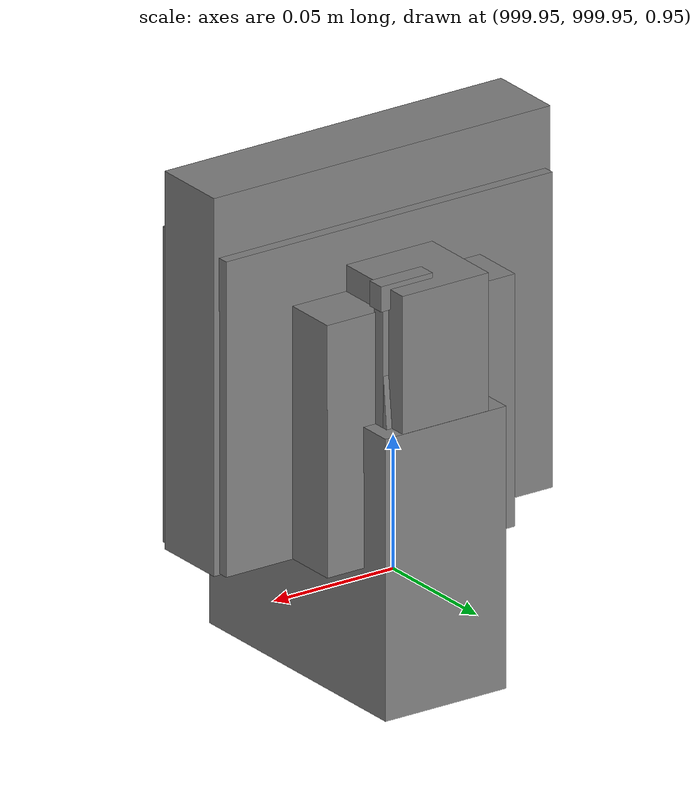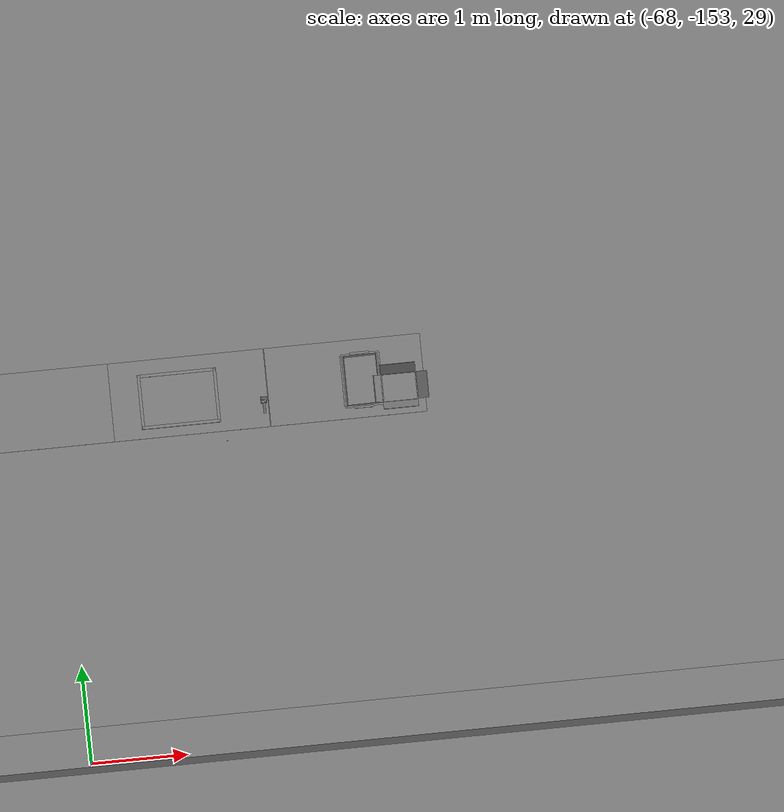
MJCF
<mujoco>
    <option gravity="0.000000000 0.000000000 -9.810000420" timestep="0.0049999999" integrator="implicitfast" density="1.225" viscosity="1.8000001e-05" noslip_iterations="10" iterations="100" sdf_iterations="50">
        <flag multiccd="disable"/>
    </option>
    <size memory="1000M"/>
    <compiler coordinate="local"/>
    <worldbody>
        <light cutoff="30" pos="0 1 1" dir="0 -1 -2"/>
        <light cutoff="30" pos="0 -1 1" dir="0 1 -2"/>
        <body pos="-64.866622925 -149.383972168 30.183746338" euler="89.999984741 89.999946594 0.000000000" name="openloong_gripper_2f85_fix_base_usda_bluebox_01">
            <geom contype="1" conaffinity="1" density="1000" type="box" material="" rgba="0.500000000 0.500000000 0.500000000 1.000000000" solimp="0.899999976 0.949999988 0.001000000" friction="1.000000000 0.005000000 0.000100000" solref="0.020000000 1.000000000" margin="0" condim="3" group="0" pos="0.276580811 0.187225342 0.000068665" quat="0.707106948 0.000077471 0.707106352 0.000077486" size="0.100000001 0.057999998 0.010000000" name="openloong_gripper_2f85_fix_base_usda_geom_5211F820_98E5_4263_800E_519E50D28677"/>
            <geom contype="1" conaffinity="1" density="1000" type="box" material="" rgba="0.500000000 0.500000000 0.500000000 1.000000000" solimp="0.899999976 0.949999988 0.001000000" friction="1.000000000 0.005000000 0.000100000" solref="0.020000000 1.000000000" margin="0" condim="3" group="0" pos="0.000000000 0.002883911 0.000000000" quat="0.999999881 0.000000000 0.000000000 0.000000000" size="0.254000008 0.003000000 0.172000006" name="openloong_gripper_2f85_fix_base_usda_geom_48442673_2B75_4018_8543_86E0E18553EE"/>
            <geom contype="1" conaffinity="1" density="1000" type="box" material="" rgba="0.500000000 0.500000000 0.500000000 1.000000000" solimp="0.899999976 0.949999988 0.001000000" friction="1.000000000 0.005000000 0.000100000" solref="0.020000000 1.000000000" margin="0" condim="3" group="0" pos="0.000000000 0.124874115 0.173484802" quat="0.999796331 0.020176515 -0.000000015 0.000000030" size="0.259999990 0.119999997 0.007000000" name="openloong_gripper_2f85_fix_base_usda_geom_71F5E267_37AA_4105_BF62_E86BE5EA5DCE"/>
            <geom contype="1" conaffinity="1" density="1000" type="box" material="" rgba="0.500000000 0.500000000 0.500000000 1.000000000" solimp="0.899999976 0.949999988 0.001000000" friction="1.000000000 0.005000000 0.000100000" solref="0.020000000 1.000000000" margin="0" condim="3" group="0" pos="0.000000000 0.124874115 -0.173469543" quat="0.999796331 -0.020176545 -0.000000015 0.000000000" size="0.259999990 0.119999997 0.007000000" name="openloong_gripper_2f85_fix_base_usda_geom_A308CD0A_6B7D_48A0_B28E_C5A07D226F7E"/>
            <geom contype="1" conaffinity="1" density="1000" type="box" material="" rgba="0.500000000 0.500000000 0.500000000 1.000000000" solimp="0.899999976 0.949999988 0.001000000" friction="1.000000000 0.005000000 0.000100000" solref="0.020000000 1.000000000" margin="0" condim="3" group="0" pos="0.000000000 0.214008331 0.188980103" quat="0.999912977 0.013176724 0.000000015 0.000000000" size="0.259999990 0.029999999 0.012500000" name="openloong_gripper_2f85_fix_base_usda_geom_8867AD28_4EA9_4A13_988D_E68DAC94AECB"/>
            <geom contype="1" conaffinity="1" density="1000" type="box" material="" rgba="0.500000000 0.500000000 0.500000000 1.000000000" solimp="0.899999976 0.949999988 0.001000000" friction="1.000000000 0.005000000 0.000100000" solref="0.020000000 1.000000000" margin="0" condim="3" group="0" pos="-0.258361816 0.125289917 0.001876831" quat="0.702796936 -0.020792112 0.710783124 0.020769298" size="0.189999998 0.119999997 0.009000000" name="openloong_gripper_2f85_fix_base_usda_geom_70252FD4_4C34_42F7_A9DE_5B4AA10ED252"/>
            <geom contype="1" conaffinity="1" density="1000" type="box" material="" rgba="0.500000000 0.500000000 0.500000000 1.000000000" solimp="0.899999976 0.949999988 0.001000000" friction="1.000000000 0.005000000 0.000100000" solref="0.020000000 1.000000000" margin="0" condim="3" group="0" pos="0.000000000 0.214008331 -0.188980103" quat="0.999912977 -0.013176769 0.000000030 0.000000015" size="0.259999990 0.029999999 0.012500000" name="openloong_gripper_2f85_fix_base_usda_geom_32ED1415_BBBE_4BBC_9D05_784F429D2BB3"/>
            <geom contype="1" conaffinity="1" density="1000" type="box" material="" rgba="0.500000000 0.500000000 0.500000000 1.000000000" solimp="0.899999976 0.949999988 0.001000000" friction="1.000000000 0.005000000 0.000100000" solref="0.020000000 1.000000000" margin="0" condim="3" group="0" pos="-0.276611328 0.187225342 0.000068665" quat="0.707106650 0.000077441 0.707106709 0.000077456" size="0.100000001 0.057999998 0.010000000" name="openloong_gripper_2f85_fix_base_usda_geom_9990511E_5338_4490_9772_995AEE5A1A01"/>
            <geom contype="1" conaffinity="1" density="1000" type="box" material="" rgba="0.500000000 0.500000000 0.500000000 1.000000000" solimp="0.899999976 0.949999988 0.001000000" friction="1.000000000 0.005000000 0.000100000" solref="0.020000000 1.000000000" margin="0" condim="3" group="0" pos="0.258331299 0.125289917 0.001876831" quat="0.702851415 0.018856421 0.710823774 -0.019329369" size="0.189999998 0.119999997 0.009000000" name="openloong_gripper_2f85_fix_base_usda_geom_F85C8336_42DF_4550_98C0_C30E1BDB2C25"/>
            <freejoint name="openloong_gripper_2f85_fix_base_usda_bluebox_01_joint"/>
            <site size="0.005000000 0.005000000 0.005000000" rgba="0.500000000 0.500000000 0.500000000 1.000000000" pos="0.000000000 0.000000000 0.000000000" quat="0.999961913 0.008726534 0.000000000 0.000000000" group="0" type="sphere" name="openloong_gripper_2f85_fix_base_usda_bluebox_01site"/>
        </body>
        <body pos="-64.496299744 -149.491867065 30.235729218" euler="0.000000000 0.000000000 89.999946594" name="openloong_gripper_2f85_fix_base_usda_cardboardbox_01">
            <geom contype="1" conaffinity="1" density="1000" type="box" material="" rgba="0.500000000 0.500000000 0.500000000 1.000000000" solimp="0.899999976 0.949999988 0.001000000" friction="1.000000000 0.005000000 0.000100000" solref="0.020000000 1.000000000" margin="0" condim="3" group="0" pos="-0.003166199 -0.004086494 0.005052090" quat="1.000000000 0.000000000 0.000000000 0.000000000" size="0.142499998 0.177500010 0.005000000" name="openloong_gripper_2f85_fix_base_usda_geom_CCE777E5_83A8_4A43_AE82_83EB3ABE8A00"/>
            <geom contype="1" conaffinity="1" density="1000" type="box" material="" rgba="0.500000000 0.500000000 0.500000000 1.000000000" solimp="0.899999976 0.949999988 0.001000000" friction="1.000000000 0.005000000 0.000100000" solref="0.020000000 1.000000000" margin="0" condim="3" group="0" pos="-0.003166199 0.170316696 0.150570869" quat="1.000000000 0.000000000 0.000000000 0.000000000" size="0.142499998 0.005000000 0.149999991" name="openloong_gripper_2f85_fix_base_usda_geom_48784003_C6FB_4BF5_9955_DAC2AB51901F"/>
            <geom contype="1" conaffinity="1" density="1000" type="box" material="" rgba="0.500000000 0.500000000 0.500000000 1.000000000" solimp="0.899999976 0.949999988 0.001000000" friction="1.000000000 0.005000000 0.000100000" solref="0.020000000 1.000000000" margin="0" condim="3" group="0" pos="-0.147399902 -0.005307198 0.150570869" quat="1.000000000 0.000000000 0.000000000 0.000000000" size="0.005000000 0.177500010 0.149999991" name="openloong_gripper_2f85_fix_base_usda_geom_A94420B0_3E48_472A_A446_E60D15FF0084"/>
            <geom contype="1" conaffinity="1" density="1000" type="box" material="" rgba="0.500000000 0.500000000 0.500000000 1.000000000" solimp="0.899999976 0.949999988 0.001000000" friction="1.000000000 0.005000000 0.000100000" solref="0.020000000 1.000000000" margin="0" condim="3" group="0" pos="0.140275955 -0.005307198 0.150570869" quat="1.000000000 0.000000000 0.000000000 0.000000000" size="0.005000000 0.177500010 0.149999991" name="openloong_gripper_2f85_fix_base_usda_geom_E0E118A2_5C79_4C9B_9EF8_07BEB8E59ECB"/>
            <geom contype="1" conaffinity="1" density="1000" type="box" material="" rgba="0.500000000 0.500000000 0.500000000 1.000000000" solimp="0.899999976 0.949999988 0.001000000" friction="1.000000000 0.005000000 0.000100000" solref="0.020000000 1.000000000" margin="0" condim="3" group="0" pos="-0.003166199 -0.181550980 0.150570869" quat="1.000000000 0.000000000 0.000000000 0.000000000" size="0.142499998 0.005000000 0.149999991" name="openloong_gripper_2f85_fix_base_usda_geom_BCE9C9EE_9B79_4161_9DE4_A8FA33D50BC7"/>
            <freejoint name="openloong_gripper_2f85_fix_base_usda_cardboardbox_01_joint"/>
            <site size="0.005000000 0.005000000 0.005000000" rgba="0.500000000 0.500000000 0.500000000 1.000000000" pos="0.000000000 0.000000000 0.000000000" quat="0.999961913 0.008726535 0.000000000 0.000000000" group="0" type="sphere" name="openloong_gripper_2f85_fix_base_usda_site_691CBD1D_25D9_48DA_8A75_30C1C4BEF6B1"/>
            <body pos="0.139160156 -0.004048347 0.301930904" euler="-179.999954224 49.383502960 179.999954224" name="openloong_gripper_2f85_fix_base_usda_A1_006">
                <geom contype="1" conaffinity="1" density="1000" type="box" material="" rgba="0.500000000 0.500000000 0.500000000 1.000000000" solimp="0.899999976 0.949999988 0.001000000" friction="1.000000000 0.005000000 0.000100000" solref="0.020000000 1.000000000" margin="0" condim="3" group="0" pos="-0.071587563 0.000009537 0.001745224" quat="0.999999881 0.000000000 0.000000000 0.000000000" size="0.071249999 0.179999992 0.002500000" name="openloong_gripper_2f85_fix_base_usda_geom_15748144_4F43_4319_BDDC_6FCD305A0760"/>
                <joint armature="0" stiffness="0.07" damping="0.0099999998" axis="0.000000 1.000000 0.000000" type="hinge" name="openloong_gripper_2f85_fix_base_usda_A1_006"/>
            </body>
            <body pos="-0.145902634 -0.004086494 0.301938057" euler="-180.000000000 -60.000011444 -180.000000000" name="openloong_gripper_2f85_fix_base_usda_A2_006">
                <geom contype="1" conaffinity="1" density="1000" type="box" material="" rgba="0.500000000 0.500000000 0.500000000 1.000000000" solimp="0.899999976 0.949999988 0.001000000" friction="1.000000000 0.005000000 0.000100000" solref="0.020000000 1.000000000" margin="0" condim="3" group="0" pos="0.071268082 0.000009537 0.002717972" quat="0.000002921 0.000000000 -0.000000030 0.999999881" size="0.071249999 0.179999992 0.002500000" name="openloong_gripper_2f85_fix_base_usda_geom_23DF9F96_27F4_424D_BF14_26442A7BDAC0"/>
                <joint armature="0" stiffness="0.07" damping="0.0099999998" axis="0.000000 1.000000 0.000000" type="hinge" name="openloong_gripper_2f85_fix_base_usda_A2_006"/>
            </body>
            <body pos="-0.003385544 0.175991058 0.301930904" euler="-125.858116150 -0.000004561 0.000002331" name="openloong_gripper_2f85_fix_base_usda_B2_006">
                <geom contype="1" conaffinity="1" density="1000" type="box" material="" rgba="0.500000000 0.500000000 0.500000000 1.000000000" solimp="0.899999976 0.949999988 0.001000000" friction="1.000000000 0.005000000 0.000100000" solref="0.020000000 1.000000000" margin="0" condim="3" group="0" pos="0.000009537 -0.070939064 -0.002470016" quat="0.999614120 0.027776197 -0.000000015 0.000000030" size="0.137500003 0.064999998 0.005000000" name="openloong_gripper_2f85_fix_base_usda_geom_E1649D93_EA13_4767_A642_1830F7085E0C"/>
                <joint armature="0" stiffness="0.07" damping="0.0099999998" axis="1.000000 0.000000 0.000000" type="hinge" name="openloong_gripper_2f85_fix_base_usda_B2_006"/>
            </body>
            <body pos="-0.003385544 -0.184140205 0.301938057" euler="147.805557251 0.000000000 0.000000000" name="openloong_gripper_2f85_fix_base_usda_B1_006">
                <geom contype="1" conaffinity="1" density="1000" type="box" material="" rgba="0.500000000 0.500000000 0.500000000 1.000000000" solimp="0.899999976 0.949999988 0.001000000" friction="1.000000000 0.005000000 0.000100000" solref="0.020000000 1.000000000" margin="0" condim="3" group="0" pos="-0.000028610 0.070202351 -0.002703667" quat="0.999614179 -0.027776167 0.000000000 0.000000000" size="0.137500003 0.064999998 0.005000000" name="openloong_gripper_2f85_fix_base_usda_geom_2EC7E1F8_CF3D_47A9_8D72_0E19F465B5F4"/>
                <joint armature="0" stiffness="0.07" damping="0.0099999998" axis="1.000000 0.000000 0.000000" type="hinge" name="openloong_gripper_2f85_fix_base_usda_B1_006"/>
            </body>
        </body>
        <body pos="-65.882858276 -149.481979370 30.229999542" euler="-64.487716675 0.000000000 0.000000000" name="openloong_gripper_2f85_fix_base_usda_Barcode">
            <geom contype="1" conaffinity="1" density="1000" type="box" material="" rgba="0.500000000 0.500000000 0.500000000 1.000000000" solimp="0.899999976 0.949999988 0.001000000" friction="1.000000000 0.005000000 0.000100000" solref="0.020000000 1.000000000" margin="0" condim="3" group="0" pos="0.000000000 0.013038635 0.001419067" quat="0.000000000 0.000000000 0.000000000 1.000000119" size="0.034000002 0.010000000 0.017999999" name="openloong_gripper_2f85_fix_base_usda_geom_F57FF642_7C6D_4189_934F_2BFF11CBCAE1"/>
            <geom contype="1" conaffinity="1" density="1000" type="box" material="" rgba="0.500000000 0.500000000 0.500000000 1.000000000" solimp="0.899999976 0.949999988 0.001000000" friction="1.000000000 0.005000000 0.000100000" solref="0.020000000 1.000000000" margin="0" condim="3" group="0" pos="0.000000000 -0.035301208 -0.007095337" quat="0.000000000 0.000000000 -0.043619365 0.999048233" size="0.028999999 0.010000000 0.020000000" name="openloong_gripper_2f85_fix_base_usda_geom_46AD425E_7B67_4629_AFDA_F31E8062AA6B"/>
            <geom contype="1" conaffinity="1" density="1000" type="box" material="" rgba="0.500000000 0.500000000 0.500000000 1.000000000" solimp="0.899999976 0.949999988 0.001000000" friction="1.000000000 0.005000000 0.000100000" solref="0.020000000 1.000000000" margin="0" condim="3" group="0" pos="0.000000000 -0.043411255 -0.011749268" quat="0.922262907 0.386563420 0.000000000 0.000000000" size="0.026000001 0.010000000 0.020000000" name="openloong_gripper_2f85_fix_base_usda_geom_3778E368_629E_4598_ADD2_3D119D44E868"/>
            <geom contype="1" conaffinity="1" density="1000" type="box" material="" rgba="0.500000000 0.500000000 0.500000000 1.000000000" solimp="0.899999976 0.949999988 0.001000000" friction="1.000000000 0.005000000 0.000100000" solref="0.020000000 1.000000000" margin="0" condim="3" group="0" pos="0.000000000 -0.016967773 -0.031860352" quat="0.000000000 0.000000000 0.000000000 1.000000119" size="0.008000000 0.010000000 0.013000000" name="openloong_gripper_2f85_fix_base_usda_geom_D05FF81B_3CC3_472F_876A_2D4FD5998854"/>
            <geom contype="1" conaffinity="1" density="1000" type="box" material="" rgba="0.500000000 0.500000000 0.500000000 1.000000000" solimp="0.899999976 0.949999988 0.001000000" friction="1.000000000 0.005000000 0.000100000" solref="0.020000000 1.000000000" margin="0" condim="3" group="0" pos="0.000000000 -0.001869202 0.000312805" quat="0.953716993 0.300705761 0.000000000 0.000000000" size="0.032000002 0.010000000 0.018999999" name="openloong_gripper_2f85_fix_base_usda_geom_5FEC41CC_2C9C_4DA0_9BEB_29FEA2657F11"/>
            <geom contype="1" conaffinity="1" density="1000" type="box" material="" rgba="0.500000000 0.500000000 0.500000000 1.000000000" solimp="0.899999976 0.949999988 0.001000000" friction="1.000000000 0.005000000 0.000100000" solref="0.020000000 1.000000000" margin="0" condim="3" group="0" pos="0.000000000 -0.019531250 -0.003173828" quat="0.953716993 0.300705761 0.000000000 0.000000000" size="0.030999999 0.010000000 0.020000000" name="openloong_gripper_2f85_fix_base_usda_geom_F578B112_045E_49EA_9CBE_36627E756DFF"/>
            <geom contype="1" conaffinity="1" density="1000" type="box" material="" rgba="0.500000000 0.500000000 0.500000000 1.000000000" solimp="0.899999976 0.949999988 0.001000000" friction="1.000000000 0.005000000 0.000100000" solref="0.020000000 1.000000000" margin="0" condim="3" group="0" pos="0.000000000 -0.035301208 -0.007095337" quat="0.953716993 0.300705761 0.000000000 0.000000000" size="0.028999999 0.010000000 0.020000000" name="openloong_gripper_2f85_fix_base_usda_geom_69D47439_6858_45EE_8304_072B960AA26C"/>
            <geom contype="1" conaffinity="1" density="1000" type="box" material="" rgba="0.500000000 0.500000000 0.500000000 1.000000000" solimp="0.899999976 0.949999988 0.001000000" friction="1.000000000 0.005000000 0.000100000" solref="0.020000000 1.000000000" margin="0" condim="3" group="0" pos="0.000000000 -0.042617798 -0.071121216" quat="0.000000000 0.000000000 0.000000000 1.000000119" size="0.013000000 0.021000000 0.059999999" name="openloong_gripper_2f85_fix_base_usda_geom_793A5236_FAD8_432D_837D_2A58034B8538"/>
            <freejoint name="openloong_gripper_2f85_fix_base_usda_Barcode_joint"/>
            <site size="0.005000000 0.005000000 0.005000000" rgba="0.500000000 0.500000000 0.500000000 1.000000000" pos="0.000000000 0.000000000 0.000000000" quat="1.000000000 0.000000000 0.000000000 0.000000000" group="0" type="sphere" name="openloong_gripper_2f85_fix_base_usda_Barcode_site"/>
        </body>
        <body pos="-66.745018005 -149.392349243 30.184000015" euler="0.000000000 0.000000000 89.999946594" name="[22329891671099]_Basket_01">
            <geom contype="1" conaffinity="1" density="1000" type="box" material="" rgba="0.500000000 0.500000000 0.500000000 1.000000000" solimp="0.899999976 0.949999988 0.001000000" friction="1.000000000 0.005000000 0.000100000" solref="0.020000000 1.000000000" margin="0" condim="3" group="0" pos="-0.052425385 0.389207840 0.089787483" quat="0.707107008 0.000000000 0.000000000 0.707106411" size="0.014249999 0.014249999 0.059999999" name="[22329891671099]_geom_744907CF_3FEE_46B3_B2FB_93F32FCFD0B5"/>
            <geom contype="1" conaffinity="1" density="1000" type="box" material="" rgba="0.500000000 0.500000000 0.500000000 1.000000000" solimp="0.899999976 0.949999988 0.001000000" friction="1.000000000 0.005000000 0.000100000" solref="0.020000000 1.000000000" margin="0" condim="3" group="0" pos="0.264015198 -0.133043289 0.089787483" quat="0.707107008 0.000000000 0.000000000 0.707106411" size="0.014249999 0.014249999 0.059999999" name="[22329891671099]_geom_8B5D4F65_0673_4317_9F02_E206824D9CF7"/>
            <geom contype="1" conaffinity="1" density="1000" type="box" material="" rgba="0.500000000 0.500000000 0.500000000 1.000000000" solimp="0.899999976 0.949999988 0.001000000" friction="1.000000000 0.005000000 0.000100000" solref="0.020000000 1.000000000" margin="0" condim="3" group="0" pos="-0.264015198 -0.265548706 0.089793205" quat="0.707107008 0.000000000 0.000000000 0.707106411" size="0.014249999 0.014249999 0.059999999" name="[22329891671099]_geom_80CEFDDC_2E55_4880_BF91_6F5B11FACD03"/>
            <geom contype="1" conaffinity="1" density="1000" type="box" material="" rgba="0.500000000 0.500000000 0.500000000 1.000000000" solimp="0.899999976 0.949999988 0.001000000" friction="1.000000000 0.005000000 0.000100000" solref="0.020000000 1.000000000" margin="0" condim="3" group="0" pos="-0.160263062 -0.389322281 0.089793205" quat="0.707107008 0.000000000 0.000000000 0.707106411" size="0.014249999 0.014249999 0.059999999" name="[22329891671099]_geom_B1E377C0_3703_4E6C_B3F7_CE0A1ABECB65"/>
            <geom contype="1" conaffinity="1" density="1000" type="box" material="" rgba="0.500000000 0.500000000 0.500000000 1.000000000" solimp="0.899999976 0.949999988 0.001000000" friction="1.000000000 0.005000000 0.000100000" solref="0.020000000 1.000000000" margin="0" condim="3" group="0" pos="0.162265778 -0.389322281 0.089787483" quat="0.707107008 0.000000000 0.000000000 0.707106411" size="0.014249999 0.014249999 0.059999999" name="[22329891671099]_geom_7EA1A206_7091_4A44_855F_51F05CD62FE0"/>
            <geom contype="1" conaffinity="1" density="1000" type="box" material="" rgba="0.500000000 0.500000000 0.500000000 1.000000000" solimp="0.899999976 0.949999988 0.001000000" friction="1.000000000 0.005000000 0.000100000" solref="0.020000000 1.000000000" margin="0" condim="3" group="0" pos="0.264015198 0.389207840 0.089787483" quat="0.707107008 0.000000000 0.000000000 0.707106411" size="0.014249999 0.014249999 0.059999999" name="[22329891671099]_geom_F1CD43F8_0F9C_41C1_A998_C4051E7CFFB0"/>
            <geom contype="1" conaffinity="1" density="1000" type="box" material="" rgba="0.500000000 0.500000000 0.500000000 1.000000000" solimp="0.899999976 0.949999988 0.001000000" friction="1.000000000 0.005000000 0.000100000" solref="0.020000000 1.000000000" margin="0" condim="3" group="0" pos="-0.264015198 -0.133043289 0.089793205" quat="0.707107008 0.000000000 0.000000000 0.707106411" size="0.014249999 0.014249999 0.059999999" name="[22329891671099]_geom_F0C5BBA1_77BC_4FE0_86D8_230CFCC26DE8"/>
            <geom contype="1" conaffinity="1" density="1000" type="box" material="" rgba="0.500000000 0.500000000 0.500000000 1.000000000" solimp="0.899999976 0.949999988 0.001000000" friction="1.000000000 0.005000000 0.000100000" solref="0.020000000 1.000000000" margin="0" condim="3" group="0" pos="-0.264026642 0.269256592 0.089793205" quat="0.707107008 0.000000000 0.000000000 0.707106411" size="0.014249999 0.014249999 0.059999999" name="[22329891671099]_geom_08F213AC_1DB0_4569_B6A2_81582236BAFF"/>
            <geom contype="1" conaffinity="1" density="1000" type="box" material="" rgba="0.500000000 0.500000000 0.500000000 1.000000000" solimp="0.899999976 0.949999988 0.001000000" friction="1.000000000 0.005000000 0.000100000" solref="0.020000000 1.000000000" margin="0" condim="3" group="0" pos="0.054462433 0.389207840 0.089787483" quat="0.707107008 0.000000000 0.000000000 0.707106411" size="0.014249999 0.014249999 0.059999999" name="[22329891671099]_geom_A15642AB_F22A_471B_AC68_8E4648164DBD"/>
            <geom contype="1" conaffinity="1" density="1000" type="box" material="" rgba="0.500000000 0.500000000 0.500000000 1.000000000" solimp="0.899999976 0.949999988 0.001000000" friction="1.000000000 0.005000000 0.000100000" solref="0.020000000 1.000000000" margin="0" condim="3" group="0" pos="0.054462433 -0.389322281 0.089787483" quat="0.707107008 0.000000000 0.000000000 0.707106411" size="0.014249999 0.014249999 0.059999999" name="[22329891671099]_geom_A25E413F_E644_4C57_A795_5778A05E8D69"/>
            <geom contype="1" conaffinity="1" density="1000" type="box" material="" rgba="0.500000000 0.500000000 0.500000000 1.000000000" solimp="0.899999976 0.949999988 0.001000000" friction="1.000000000 0.005000000 0.000100000" solref="0.020000000 1.000000000" margin="0" condim="3" group="0" pos="0.264015198 0.269256592 0.089793205" quat="0.707107008 0.000000000 0.000000000 0.707106411" size="0.014249999 0.014249999 0.059999999" name="[22329891671099]_geom_73A84E2A_1098_4589_A24E_E7E645757C51"/>
            <geom contype="1" conaffinity="1" density="1000" type="box" material="" rgba="0.500000000 0.500000000 0.500000000 1.000000000" solimp="0.899999976 0.949999988 0.001000000" friction="1.000000000 0.005000000 0.000100000" solref="0.020000000 1.000000000" margin="0" condim="3" group="0" pos="0.264015198 -0.389322281 0.089787483" quat="0.707107008 0.000000000 0.000000000 0.707106411" size="0.014249999 0.014249999 0.059999999" name="[22329891671099]_geom_56F337A6_5F63_48B5_B690_5F458E05B328"/>
            <geom contype="1" conaffinity="1" density="1000" type="box" material="" rgba="0.500000000 0.500000000 0.500000000 1.000000000" solimp="0.899999976 0.949999988 0.001000000" friction="1.000000000 0.005000000 0.000100000" solref="0.020000000 1.000000000" margin="0" condim="3" group="0" pos="0.000000000 0.000000000 0.015998840" quat="0.707107008 0.000000000 0.000000000 0.707106411" size="0.403499991 0.279000014 0.015750000" name="[22329891671099]_geom_86DABC32_55DA_446F_B85C_88D21A059060"/>
            <geom contype="1" conaffinity="1" density="1000" type="box" material="" rgba="0.500000000 0.500000000 0.500000000 1.000000000" solimp="0.899999976 0.949999988 0.001000000" friction="1.000000000 0.005000000 0.000100000" solref="0.020000000 1.000000000" margin="0" condim="3" group="0" pos="0.000000000 -0.389476776 0.163619041" quat="0.707107008 0.000000000 0.000000000 0.707106411" size="0.015000000 0.277500004 0.015750000" name="[22329891671099]_geom_BC6C718C_783F_4E93_A705_7499E15F2EAA"/>
            <geom contype="1" conaffinity="1" density="1000" type="box" material="" rgba="0.500000000 0.500000000 0.500000000 1.000000000" solimp="0.899999976 0.949999988 0.001000000" friction="1.000000000 0.005000000 0.000100000" solref="0.020000000 1.000000000" margin="0" condim="3" group="0" pos="0.162265778 0.389207840 0.089787483" quat="0.707107008 0.000000000 0.000000000 0.707106411" size="0.014249999 0.014249999 0.059999999" name="[22329891671099]_geom_31B816BA_1674_48D9_A4F1_F64A9F0E7AC5"/>
            <geom contype="1" conaffinity="1" density="1000" type="box" material="" rgba="0.500000000 0.500000000 0.500000000 1.000000000" solimp="0.899999976 0.949999988 0.001000000" friction="1.000000000 0.005000000 0.000100000" solref="0.020000000 1.000000000" margin="0" condim="3" group="0" pos="0.000000000 0.389471054 0.163619041" quat="0.707107008 0.000000000 0.000000000 0.707106411" size="0.015000000 0.277500004 0.015750000" name="[22329891671099]_geom_D647993A_A371_41DD_819B_AD446965AA01"/>
            <geom contype="1" conaffinity="1" density="1000" type="box" material="" rgba="0.500000000 0.500000000 0.500000000 1.000000000" solimp="0.899999976 0.949999988 0.001000000" friction="1.000000000 0.005000000 0.000100000" solref="0.020000000 1.000000000" margin="0" condim="3" group="0" pos="-0.263511658 0.000000000 0.163619041" quat="0.707107008 0.000000000 0.000000000 0.707106411" size="0.403499991 0.015000000 0.015750000" name="[22329891671099]_geom_DF1EA8A6_4463_408E_857B_F63AA140891F"/>
            <geom contype="1" conaffinity="1" density="1000" type="box" material="" rgba="0.500000000 0.500000000 0.500000000 1.000000000" solimp="0.899999976 0.949999988 0.001000000" friction="1.000000000 0.005000000 0.000100000" solref="0.020000000 1.000000000" margin="0" condim="3" group="0" pos="-0.264015198 0.141334534 0.089793205" quat="0.707107008 0.000000000 0.000000000 0.707106411" size="0.014249999 0.014249999 0.059999999" name="[22329891671099]_geom_526CCE46_F008_4E2F_9C74_12243FEA96B0"/>
            <geom contype="1" conaffinity="1" density="1000" type="box" material="" rgba="0.500000000 0.500000000 0.500000000 1.000000000" solimp="0.899999976 0.949999988 0.001000000" friction="1.000000000 0.005000000 0.000100000" solref="0.020000000 1.000000000" margin="0" condim="3" group="0" pos="0.264015198 -0.265548706 0.089787483" quat="0.707107008 0.000000000 0.000000000 0.707106411" size="0.014249999 0.014249999 0.059999999" name="[22329891671099]_geom_4D33D44D_E47D_402A_BE8E_3E7CE93BDE9C"/>
            <geom contype="1" conaffinity="1" density="1000" type="box" material="" rgba="0.500000000 0.500000000 0.500000000 1.000000000" solimp="0.899999976 0.949999988 0.001000000" friction="1.000000000 0.005000000 0.000100000" solref="0.020000000 1.000000000" margin="0" condim="3" group="0" pos="-0.160263062 0.389207840 0.089787483" quat="0.707107008 0.000000000 0.000000000 0.707106411" size="0.014249999 0.014249999 0.059999999" name="[22329891671099]_geom_CE95CD79_84B5_4831_83E8_C4A71AD740AB"/>
            <geom contype="1" conaffinity="1" density="1000" type="box" material="" rgba="0.500000000 0.500000000 0.500000000 1.000000000" solimp="0.899999976 0.949999988 0.001000000" friction="1.000000000 0.005000000 0.000100000" solref="0.020000000 1.000000000" margin="0" condim="3" group="0" pos="-0.052425385 -0.389322281 0.089787483" quat="0.707107008 0.000000000 0.000000000 0.707106411" size="0.014249999 0.014249999 0.059999999" name="[22329891671099]_geom_E45B4370_C76B_43F3_B69B_201A482655C9"/>
            <geom contype="1" conaffinity="1" density="1000" type="box" material="" rgba="0.500000000 0.500000000 0.500000000 1.000000000" solimp="0.899999976 0.949999988 0.001000000" friction="1.000000000 0.005000000 0.000100000" solref="0.020000000 1.000000000" margin="0" condim="3" group="0" pos="-0.264026642 -0.389322281 0.089793205" quat="0.707107008 0.000000000 0.000000000 0.707106411" size="0.014249999 0.014249999 0.059999999" name="[22329891671099]_geom_D0E600DE_1C55_4492_9782_F5663E43719F"/>
            <geom contype="1" conaffinity="1" density="1000" type="box" material="" rgba="0.500000000 0.500000000 0.500000000 1.000000000" solimp="0.899999976 0.949999988 0.001000000" friction="1.000000000 0.005000000 0.000100000" solref="0.020000000 1.000000000" margin="0" condim="3" group="0" pos="0.264015198 0.141334534 0.089787483" quat="0.707107008 0.000000000 0.000000000 0.707106411" size="0.014249999 0.014249999 0.059999999" name="[22329891671099]_geom_C055E8D1_CBC5_42A5_8A91_761540F06726"/>
            <geom contype="1" conaffinity="1" density="1000" type="box" material="" rgba="0.500000000 0.500000000 0.500000000 1.000000000" solimp="0.899999976 0.949999988 0.001000000" friction="1.000000000 0.005000000 0.000100000" solref="0.020000000 1.000000000" margin="0" condim="3" group="0" pos="-0.264015198 0.389207840 0.089793205" quat="0.707107008 0.000000000 0.000000000 0.707106411" size="0.014249999 0.014249999 0.059999999" name="[22329891671099]_geom_C91C1BEB_53BC_409A_99F1_9D07675B56B6"/>
            <geom contype="1" conaffinity="1" density="1000" type="box" material="" rgba="0.500000000 0.500000000 0.500000000 1.000000000" solimp="0.899999976 0.949999988 0.001000000" friction="1.000000000 0.005000000 0.000100000" solref="0.020000000 1.000000000" margin="0" condim="3" group="0" pos="0.264015198 0.004480362 0.089787483" quat="0.707107008 0.000000000 0.000000000 0.707106411" size="0.014249999 0.014249999 0.059999999" name="[22329891671099]_geom_610BBBA0_8D88_4621_8D54_34A8263A3D7C"/>
            <geom contype="1" conaffinity="1" density="1000" type="box" material="" rgba="0.500000000 0.500000000 0.500000000 1.000000000" solimp="0.899999976 0.949999988 0.001000000" friction="1.000000000 0.005000000 0.000100000" solref="0.020000000 1.000000000" margin="0" condim="3" group="0" pos="0.263694763 -0.000011444 0.163619041" quat="0.707107008 0.000000000 0.000000000 0.707106411" size="0.403499991 0.015000000 0.015750000" name="[22329891671099]_geom_67199095_093C_428E_828C_662A73D09AB6"/>
            <geom contype="1" conaffinity="1" density="1000" type="box" material="" rgba="0.500000000 0.500000000 0.500000000 1.000000000" solimp="0.899999976 0.949999988 0.001000000" friction="1.000000000 0.005000000 0.000100000" solref="0.020000000 1.000000000" margin="0" condim="3" group="0" pos="-0.264015198 0.004480362 0.089793205" quat="0.707107008 0.000000000 0.000000000 0.707106411" size="0.014249999 0.014249999 0.059999999" name="[22329891671099]_geom_E64CD412_7469_47BE_82AB_BD55A5FE85E1"/>
            <freejoint name="[22329891671099]_joint_D3B9108C_B6FB_444A_9ACB_7EB8BC4AA637"/>
        </body>
        <body pos="0.000000000 0.000000000 0.000000000" euler="0.000000000 0.000000000 0.000000000" name="Static Objects_Static Objects">
            <geom contype="1" conaffinity="1" density="1000" type="box" material="" rgba="0.500000000 0.500000000 0.500000000 1.000000000" solimp="0.899999976 0.949999988 0.001000000" friction="1.000000000 0.005000000 0.000100000" solref="0.020000000 1.000000000" margin="0" condim="3" group="0" pos="-67.544113159 -149.365814209 29.727830887" quat="0.500000417 0.499999970 0.499999553 0.499999970" size="0.381000012 0.319999993 0.041000001" name="Static Objects_geom_10596DAB_1322_4AC2_B87A_97A3872BEA73"/>
            <geom contype="1" conaffinity="1" density="1000" type="box" material="" rgba="0.500000000 0.500000000 0.500000000 1.000000000" solimp="0.899999976 0.949999988 0.001000000" friction="1.000000000 0.005000000 0.000100000" solref="0.020000000 1.000000000" margin="0" condim="3" group="0" pos="-68.239501953 -149.365814209 30.086868286" quat="0.500000417 0.499999970 0.499999553 0.499999970" size="0.370999992 0.039500002 0.745000005" name="Static Objects_geom_841FCB00_BA60_4382_AFF0_7ED881F6D0FC"/>
            <geom contype="1" conaffinity="1" density="1000" type="box" material="" rgba="0.500000000 0.500000000 0.500000000 1.000000000" solimp="0.899999976 0.949999988 0.001000000" friction="1.000000000 0.005000000 0.000100000" solref="0.020000000 1.000000000" margin="0" condim="3" group="0" pos="-68.239501953 -149.365814209 30.147235870" quat="0.500000417 0.499999970 0.499999553 0.499999970" size="0.400000006 0.022000000 0.800000012" name="Static Objects_geom_024100EB_ABCB_49FE_A065_78223508A7F7"/>
            <geom contype="1" conaffinity="1" density="1000" type="box" material="" rgba="0.500000000 0.500000000 0.500000000 1.000000000" solimp="0.899999976 0.949999988 0.001000000" friction="1.000000000 0.005000000 0.000100000" solref="0.020000000 1.000000000" margin="0" condim="3" group="0" pos="-68.934890747 -149.365814209 29.727830887" quat="0.500000417 0.499999970 0.499999553 0.499999970" size="0.381000012 0.319999993 0.041000001" name="Static Objects_geom_F7759C32_7F7E_48BA_B31E_50208A2382C3"/>
            <geom contype="1" conaffinity="1" density="1000" type="box" material="" rgba="0.500000000 0.500000000 0.500000000 1.000000000" solimp="0.899999976 0.949999988 0.001000000" friction="1.000000000 0.005000000 0.000100000" solref="0.020000000 1.000000000" margin="0" condim="3" group="0" pos="-68.239501953 -149.365814209 29.561563492" quat="0.500000417 0.499999970 0.499999553 0.499999970" size="0.020000000 0.022000000 0.660000026" name="Static Objects_geom_811B2BAF_5E64_4315_B733_2DD06F7603A8"/>
            <geom contype="1" conaffinity="1" density="1000" type="box" material="" rgba="0.500000000 0.500000000 0.500000000 1.000000000" solimp="0.899999976 0.949999988 0.001000000" friction="1.000000000 0.005000000 0.000100000" solref="0.020000000 1.000000000" margin="0" condim="3" group="0" pos="-65.945671082 -149.365814209 29.727830887" quat="0.500000417 0.499999970 0.499999553 0.499999970" size="0.381000012 0.319999993 0.041000001" name="Static Objects_geom_9BD0563F_E4E5_4D43_B28F_921024EF24DE"/>
            <geom contype="1" conaffinity="1" density="1000" type="box" material="" rgba="0.500000000 0.500000000 0.500000000 1.000000000" solimp="0.899999976 0.949999988 0.001000000" friction="1.000000000 0.005000000 0.000100000" solref="0.020000000 1.000000000" margin="0" condim="3" group="0" pos="-66.641059875 -149.365814209 30.086868286" quat="0.500000417 0.499999970 0.499999553 0.499999970" size="0.370999992 0.039500002 0.745000005" name="Static Objects_geom_06F608D7_2D54_4E70_B33F_6A658B901B62"/>
            <geom contype="1" conaffinity="1" density="1000" type="box" material="" rgba="0.500000000 0.500000000 0.500000000 1.000000000" solimp="0.899999976 0.949999988 0.001000000" friction="1.000000000 0.005000000 0.000100000" solref="0.020000000 1.000000000" margin="0" condim="3" group="0" pos="-66.641059875 -149.365814209 30.147235870" quat="0.500000417 0.499999970 0.499999553 0.499999970" size="0.400000006 0.022000000 0.800000012" name="Static Objects_geom_FE4BF651_E2FC_4000_BACF_781D18B96D0B"/>
            <geom contype="1" conaffinity="1" density="1000" type="box" material="" rgba="0.500000000 0.500000000 0.500000000 1.000000000" solimp="0.899999976 0.949999988 0.001000000" friction="1.000000000 0.005000000 0.000100000" solref="0.020000000 1.000000000" margin="0" condim="3" group="0" pos="-67.336448669 -149.365814209 29.727830887" quat="0.500000417 0.499999970 0.499999553 0.499999970" size="0.381000012 0.319999993 0.041000001" name="Static Objects_geom_1C30D3A1_7874_48D1_B917_75C4A21AF03B"/>
            <geom contype="1" conaffinity="1" density="1000" type="box" material="" rgba="0.500000000 0.500000000 0.500000000 1.000000000" solimp="0.899999976 0.949999988 0.001000000" friction="1.000000000 0.005000000 0.000100000" solref="0.020000000 1.000000000" margin="0" condim="3" group="0" pos="-66.641059875 -149.365814209 29.561563492" quat="0.500000417 0.499999970 0.499999553 0.499999970" size="0.020000000 0.022000000 0.660000026" name="Static Objects_geom_92784E71_BA92_4BC3_8611_76253D84AF2A"/>
            <geom contype="1" conaffinity="1" density="1000" type="box" material="" rgba="0.500000000 0.500000000 0.500000000 1.000000000" solimp="0.899999976 0.949999988 0.001000000" friction="1.000000000 0.005000000 0.000100000" solref="0.020000000 1.000000000" margin="0" condim="3" group="0" pos="-64.338577271 -149.365814209 29.727830887" quat="0.500000417 0.499999970 0.499999553 0.499999970" size="0.381000012 0.319999993 0.041000001" name="Static Objects_geom_568F02C9_6209_4326_9CC8_26DD36DC0738"/>
            <geom contype="1" conaffinity="1" density="1000" type="box" material="" rgba="0.500000000 0.500000000 0.500000000 1.000000000" solimp="0.899999976 0.949999988 0.001000000" friction="1.000000000 0.005000000 0.000100000" solref="0.020000000 1.000000000" margin="0" condim="3" group="0" pos="-65.033966064 -149.365814209 30.086868286" quat="0.500000417 0.499999970 0.499999553 0.499999970" size="0.370999992 0.039500002 0.745000005" name="Static Objects_geom_8386D3C6_B71C_4A00_B4D0_C3AA1915CCAB"/>
            <geom contype="1" conaffinity="1" density="1000" type="box" material="" rgba="0.500000000 0.500000000 0.500000000 1.000000000" solimp="0.899999976 0.949999988 0.001000000" friction="1.000000000 0.005000000 0.000100000" solref="0.020000000 1.000000000" margin="0" condim="3" group="0" pos="-65.033966064 -149.365814209 30.147235870" quat="0.500000417 0.499999970 0.499999553 0.499999970" size="0.400000006 0.022000000 0.800000012" name="Static Objects_geom_99B686D6_2FA7_4CB5_AE93_0796129AABE1"/>
            <geom contype="1" conaffinity="1" density="1000" type="box" material="" rgba="0.500000000 0.500000000 0.500000000 1.000000000" solimp="0.899999976 0.949999988 0.001000000" friction="1.000000000 0.005000000 0.000100000" solref="0.020000000 1.000000000" margin="0" condim="3" group="0" pos="-65.729354858 -149.365814209 29.727830887" quat="0.500000417 0.499999970 0.499999553 0.499999970" size="0.381000012 0.319999993 0.041000001" name="Static Objects_geom_82E30DC7_8BA9_477F_91DD_3706EA30183F"/>
            <geom contype="1" conaffinity="1" density="1000" type="box" material="" rgba="0.500000000 0.500000000 0.500000000 1.000000000" solimp="0.899999976 0.949999988 0.001000000" friction="1.000000000 0.005000000 0.000100000" solref="0.020000000 1.000000000" margin="0" condim="3" group="0" pos="-65.033966064 -149.365814209 29.561563492" quat="0.500000417 0.499999970 0.499999553 0.499999970" size="0.020000000 0.022000000 0.660000026" name="Static Objects_geom_E7A4FCD4_1511_4491_8C22_3BEC142602FD"/>
            <geom contype="1" conaffinity="1" density="1000" type="box" material="" rgba="0.500000000 0.500000000 0.500000000 1.000000000" solimp="0.899999976 0.949999988 0.001000000" friction="1.000000000 0.005000000 0.000100000" solref="0.020000000 1.000000000" margin="0" condim="3" group="0" pos="-61.754566193 -137.853729248 33.906845093" quat="0.707107067 0.000000000 0.000000000 0.707106471" size="0.759999990 0.759999990 4.500000000" name="Static Objects_geom_12E39C45_73F2_4E21_9F31_6E381EC81B22"/>
            <geom contype="1" conaffinity="1" density="1000" type="box" material="" rgba="0.500000000 0.500000000 0.500000000 1.000000000" solimp="0.899999976 0.949999988 0.001000000" friction="1.000000000 0.005000000 0.000100000" solref="0.020000000 1.000000000" margin="0" condim="3" group="0" pos="-57.511135101 -144.927108765 31.707921982" quat="1.000000000 0.000000000 0.000000000 0.000000000" size="0.200000003 8.000000000 2.299999952" name="Static Objects_geom_C800488B_AE5C_475A_A1EF_690238FD23A3"/>
            <geom contype="1" conaffinity="1" density="1000" type="box" material="" rgba="0.500000000 0.500000000 0.500000000 1.000000000" solimp="0.899999976 0.949999988 0.001000000" friction="1.000000000 0.005000000 0.000100000" solref="0.020000000 1.000000000" margin="0" condim="3" group="0" pos="-80.517646790 -157.574050903 31.688196182" quat="0.707107067 0.000000000 0.000000000 0.707106471" size="0.600000024 0.600000024 2.299999952" name="Static Objects_geom_6EC517F1_4F29_4916_B01A_E2D5F4B957BD"/>
            <geom contype="1" conaffinity="1" density="1000" type="box" material="" rgba="0.500000000 0.500000000 0.500000000 1.000000000" solimp="0.899999976 0.949999988 0.001000000" friction="1.000000000 0.005000000 0.000100000" solref="0.020000000 1.000000000" margin="0" condim="3" group="0" pos="-80.711044312 -147.414932251 31.666158676" quat="1.000000000 0.000000000 0.000000000 0.000000000" size="0.200000003 10.000000000 2.299999952" name="Static Objects_geom_C70D6689_AC29_4891_A9A7_72C0498B3942"/>
            <geom contype="1" conaffinity="1" density="1000" type="box" material="" rgba="0.500000000 0.500000000 0.500000000 1.000000000" solimp="0.899999976 0.949999988 0.001000000" friction="1.000000000 0.005000000 0.000100000" solref="0.020000000 1.000000000" margin="0" condim="3" group="0" pos="-57.687217712 -137.434692383 31.688196182" quat="0.707107067 0.000000000 0.000000000 0.707106471" size="0.600000024 0.600000024 2.299999952" name="Static Objects_geom_BE749C9C_B03C_4D58_9C16_77CFB2826C4F"/>
            <geom contype="1" conaffinity="1" density="1000" type="box" material="" rgba="0.500000000 0.500000000 0.500000000 1.000000000" solimp="0.899999976 0.949999988 0.001000000" friction="1.000000000 0.005000000 0.000100000" solref="0.020000000 1.000000000" margin="0" condim="3" group="0" pos="-69.537033081 -140.263229370 31.714921951" quat="0.707107067 0.000000000 0.000000000 0.707106471" size="0.759999990 4.500000000 2.299999952" name="Static Objects_geom_EA1E03CA_5969_44CF_B8C6_E9B992B9166D"/>
            <geom contype="1" conaffinity="1" density="1000" type="box" material="" rgba="0.500000000 0.500000000 0.500000000 1.000000000" solimp="0.899999976 0.949999988 0.001000000" friction="1.000000000 0.005000000 0.000100000" solref="0.020000000 1.000000000" margin="0" condim="3" group="0" pos="-80.073638916 -137.853713989 33.906845093" quat="0.707107067 0.000000000 0.000000000 0.707106471" size="0.759999990 0.759999990 4.500000000" name="Static Objects_geom_B08822CE_565F_410F_A97A_12FF6A59AD53"/>
            <geom contype="1" conaffinity="1" density="1000" type="box" material="" rgba="0.500000000 0.500000000 0.500000000 1.000000000" solimp="0.899999976 0.949999988 0.001000000" friction="1.000000000 0.005000000 0.000100000" solref="0.020000000 1.000000000" margin="0" condim="3" group="0" pos="-73.406707764 -155.734664917 31.707921982" quat="1.000000000 0.000000000 0.000000000 0.000000000" size="0.200000003 3.000000000 2.299999952" name="Static Objects_geom_54341D55_C061_4356_9785_DF4D550983ED"/>
            <geom contype="1" conaffinity="1" density="1000" type="box" material="" rgba="0.500000000 0.500000000 0.500000000 1.000000000" solimp="0.899999976 0.949999988 0.001000000" friction="1.000000000 0.005000000 0.000100000" solref="0.020000000 1.000000000" margin="0" condim="3" group="0" pos="-68.497543335 -137.448257446 31.707921982" quat="0.707107067 0.000000000 0.000000000 0.707106471" size="0.200000003 14.000000000 2.299999952" name="Static Objects_geom_E5FB3A44_8CA3_4ECF_AC5A_ACAF48F90A9E"/>
            <geom contype="1" conaffinity="1" density="1000" type="cylinder" material="" rgba="0.500000000 0.500000000 0.500000000 1.000000000" solimp="0.899999976 0.949999988 0.001000000" friction="1.000000000 0.005000000 0.000100000" solref="0.020000000 1.000000000" margin="0" condim="3" group="0" pos="-68.868522644 -142.134506226 31.711090088" quat="0.707107067 0.000000000 0.000000000 0.707106471" size="0.509999990 2.299999952 1.000000000" name="Static Objects_geom_64AF8F2B_EE9D_4A8B_B861_7AEAA2A1F1F3"/>
            <geom contype="1" conaffinity="1" density="1000" type="plane" material="" rgba="0.500000000 0.500000000 0.500000000 1.000000000" solimp="0.899999976 0.949999988 0.001000000" friction="1.000000000 0.005000000 0.000100000" solref="0.020000000 1.000000000" margin="0" condim="3" group="0" pos="-72.873703003 -147.131927490 29.409669876" quat="1.000000000 0.000000000 0.000000000 0.000000000" size="18.000000000 14.000000000 1.000000000" name="Static Objects_geom_D458551B_3F4E_4C0D_B2C3_3E20080D38AE"/>
            <geom contype="1" conaffinity="1" density="1000" type="box" material="" rgba="0.500000000 0.500000000 0.500000000 1.000000000" solimp="0.899999976 0.949999988 0.001000000" friction="1.000000000 0.005000000 0.000100000" solref="0.020000000 1.000000000" margin="0" condim="3" group="0" pos="-79.943580627 -157.782272339 31.707921982" quat="0.707107067 0.000000000 0.000000000 0.707106471" size="0.200000003 7.000000000 2.299999952" name="Static Objects_geom_363BA5EF_6B82_4094_985A_735E7F660881"/>
            <geom contype="1" conaffinity="1" density="1000" type="box" material="" rgba="0.500000000 0.500000000 0.500000000 1.000000000" solimp="0.899999976 0.949999988 0.001000000" friction="1.000000000 0.005000000 0.000100000" solref="0.020000000 1.000000000" margin="0" condim="3" group="0" pos="-65.421028137 -152.903442383 31.707921982" quat="0.707107067 0.000000000 0.000000000 0.707106471" size="0.200000003 7.800000191 2.299999952" name="Static Objects_geom_9040A3CB_84DE_4A8A_8A4A_615F283993E7"/>
            <geom contype="1" conaffinity="1" density="1000" type="box" material="" rgba="0.500000000 0.500000000 0.500000000 1.000000000" solimp="0.899999976 0.949999988 0.001000000" friction="1.000000000 0.005000000 0.000100000" solref="0.020000000 1.000000000" margin="0" condim="3" group="0" pos="-74.776908875 -149.964416504 31.688196182" quat="1.000000000 0.000000000 0.000000000 0.000000000" size="0.600000024 0.409999996 2.299999952" name="Static Objects_geom_D53C3172_041E_4CEB_AA7B_C0C9D165F569"/>
            <geom contype="1" conaffinity="1" density="1000" type="cylinder" material="" rgba="0.500000000 0.500000000 0.500000000 1.000000000" solimp="0.899999976 0.949999988 0.001000000" friction="1.000000000 0.005000000 0.000100000" solref="0.020000000 1.000000000" margin="0" condim="3" group="0" pos="-60.161884308 -142.134506226 31.711090088" quat="0.707107067 0.000000000 0.000000000 0.707106471" size="0.509999990 2.299999952 1.000000000" name="Static Objects_geom_ED0C35F2_54A5_45BF_984B_E3DEF1F31C26"/>
            <geom contype="1" conaffinity="1" density="1000" type="cylinder" material="" rgba="0.500000000 0.500000000 0.500000000 1.000000000" solimp="0.899999976 0.949999988 0.001000000" friction="1.000000000 0.005000000 0.000100000" solref="0.020000000 1.000000000" margin="0" condim="3" group="0" pos="-75.382453918 -149.963455200 31.711090088" quat="0.707107067 0.000000000 0.000000000 0.707106471" size="0.409999996 2.299999952 1.000000000" name="Static Objects_geom_8A472039_5CBC_4938_AFA9_A022616E1C6D"/>
            <geom contype="1" conaffinity="1" density="1000" type="cylinder" material="" rgba="0.500000000 0.500000000 0.500000000 1.000000000" solimp="0.899999976 0.949999988 0.001000000" friction="1.000000000 0.005000000 0.000100000" solref="0.020000000 1.000000000" margin="0" condim="3" group="0" pos="-74.154960632 -149.963455200 31.711090088" quat="0.707107067 0.000000000 0.000000000 0.707106471" size="0.409999996 2.299999952 1.000000000" name="Static Objects_geom_3DE73EC3_2183_4645_9C0E_FA6B4C07867F"/>
            <geom contype="1" conaffinity="1" density="1000" type="cylinder" material="" rgba="0.500000000 0.500000000 0.500000000 1.000000000" solimp="0.899999976 0.949999988 0.001000000" friction="1.000000000 0.005000000 0.000100000" solref="0.020000000 1.000000000" margin="0" condim="3" group="0" pos="-77.566612244 -142.134506226 31.711090088" quat="0.707107067 0.000000000 0.000000000 0.707106471" size="0.509999990 2.299999952 1.000000000" name="Static Objects_geom_BF919BD1_D622_4318_A6DF_E819F055F86E"/>
        </body>
        <body pos="1000.000000000 1000.000000000 1.000000000" euler="0.000000000 0.000000000 180.000000000" name="openloong_gripper_2f85_fix_base_usda_cpu_fan">
            <geom contype="1" conaffinity="1" density="1000" type="box" material="" rgba="0.500000000 0.500000000 0.500000000 1.000000000" solimp="0.899999976 0.949999988 0.001000000" friction="1.000000000 0.005000000 0.000100000" solref="0.020000000 1.000000000" margin="0" condim="3" group="0" pos="0.000000000 0.000000000 0.070034981" quat="0.000000000 0.000000000 0.000000000 1.000000000" size="0.070700005 0.014699999 0.070700005" name="openloong_gripper_2f85_fix_base_usda_geom_F918AD77_EE77_4C3B_A139_FCD96760916A"/>
            <freejoint name="openloong_gripper_2f85_fix_base_usda_cpu_fan_joint"/>
            <site size="0.005000000 0.005000000 0.005000000" rgba="0.500000000 0.500000000 0.500000000 1.000000000" pos="0.000000000 0.000000000 0.000000000" quat="0.999961913 0.008726535 0.000000000 0.000000000" group="0" type="sphere" name="openloong_gripper_2f85_fix_base_usda_cpu_fancsite"/>
        </body>
        <body pos="-65.887939453 -149.644714355 31.167791367" euler="40.757789612 -59.407051086 104.446266174" mocap="true" name="spotlight2_SpotLight"/>
        <body pos="1000.000000000 999.999938965 1.000000000" euler="0.000000000 0.000000000 180.000000000" name="openloong_gripper_2f85_fix_base_usda_intelcore_i5">
            <geom contype="1" conaffinity="1" density="1000" type="box" material="" rgba="0.500000000 0.500000000 0.500000000 1.000000000" solimp="0.899999976 0.949999988 0.001000000" friction="1.000000000 0.005000000 0.000100000" solref="0.020000000 1.000000000" margin="0" condim="3" group="0" pos="0.000000000 0.000000000 0.051722717" quat="0.707106709 0.000000000 0.000000000 -0.707106769" size="0.052800000 0.018080002 0.052800000" name="openloong_gripper_2f85_fix_base_usda_geom_E03CC10B_DE65_4897_99F3_E7B3A6974459"/>
            <freejoint name="openloong_gripper_2f85_fix_base_usda_intelcore_i5_joint"/>
            <site size="0.005000000 0.005000000 0.005000000" rgba="0.500000000 0.500000000 0.500000000 1.000000000" pos="0.000000000 0.000000000 0.000000000" quat="0.999961913 0.008726534 0.000000000 0.000000000" group="0" type="sphere" name="openloong_gripper_2f85_fix_base_usda_intelcore_i5site"/>
        </body>
        <body pos="1000.000000000 1000.000000000 1.000000000" euler="0.000011953 0.000005123 -179.999984741" name="openloong_gripper_2f85_fix_base_usda_intel_box">
            <geom contype="1" conaffinity="1" density="1000" type="box" material="" rgba="0.500000000 0.500000000 0.500000000 1.000000000" solimp="0.899999976 0.949999988 0.001000000" friction="1.000000000 0.005000000 0.000100000" solref="0.020000000 1.000000000" margin="0" condim="3" group="0" pos="0.000000000 -0.000067139 0.000082284" quat="0.707106709 0.000000225 0.000000253 0.707106650" size="0.052800003 0.025300000 0.052800003" name="openloong_gripper_2f85_fix_base_usda_geom_DA8F0096_1752_45DA_837F_BFA95E9B9570"/>
            <freejoint name="openloong_gripper_2f85_fix_base_usda_intel_box_joint"/>
            <site size="0.005000000 0.005000000 0.005000000" rgba="0.500000000 0.500000000 0.500000000 1.000000000" pos="0.000000000 0.000000000 0.000000000" quat="0.999961913 0.008726500 0.000000000 0.000000000" group="0" type="sphere" name="openloong_gripper_2f85_fix_base_usda_intel_boxsite"/>
        </body>
        <body pos="1000.000000000 1000.000000000 1.000000000" euler="0.000000000 0.000000000 180.000000000" name="openloong_gripper_2f85_fix_base_usda_wifi_box">
            <geom contype="1" conaffinity="1" density="1000" type="box" material="" rgba="0.500000000 0.500000000 0.500000000 1.000000000" solimp="0.899999976 0.949999988 0.001000000" friction="1.000000000 0.005000000 0.000100000" solref="0.020000000 1.000000000" margin="0" condim="3" group="0" pos="0.000000000 0.000000000 0.058978677" quat="0.000000000 0.000000047 0.000000000 1.000000000" size="0.068499997 0.018999999 0.059000000" name="openloong_gripper_2f85_fix_base_usda_geom_C9392029_66CE_48C7_B5BC_0BC442C9E9F3"/>
            <freejoint name="openloong_gripper_2f85_fix_base_usda_wifi_box_joint"/>
            <site size="0.005000000 0.005000000 0.005000000" rgba="0.500000000 0.500000000 0.500000000 1.000000000" pos="0.000000000 0.000000000 0.000000000" quat="0.999961913 0.008726500 0.000000000 0.000000000" group="0" type="sphere" name="openloong_gripper_2f85_fix_base_usda_wifi_boxsite"/>
        </body>
        <body pos="-66.149780273 -149.011459351 31.164735794" euler="138.303176880 52.744129181 -71.580703735" mocap="true" name="spotlight6_SpotLight"/>
        <body pos="1000.000000000 1000.000000000 1.000000000" euler="0.000000000 0.000000000 180.000000000" name="openloong_gripper_2f85_fix_base_usda_battery_01">
            <geom contype="1" conaffinity="1" density="1000" type="box" material="" rgba="0.500000000 0.500000000 0.500000000 1.000000000" solimp="0.899999976 0.949999988 0.001000000" friction="1.000000000 0.005000000 0.000100000" solref="0.020000000 1.000000000" margin="0" condim="3" group="0" pos="-0.011123657 -0.041940309 0.101691343" quat="1.000000000 0.000000000 0.000000000 0.000000000" size="0.010800000 0.003375000 0.004725000" name="openloong_gripper_2f85_fix_base_usda_geom_CE31551F_F806_4915_91C9_EDDDCA190185"/>
            <geom contype="1" conaffinity="1" density="1000" type="box" material="" rgba="0.500000000 0.500000000 0.500000000 1.000000000" solimp="0.899999976 0.949999988 0.001000000" friction="1.000000000 0.005000000 0.000100000" solref="0.020000000 1.000000000" margin="0" condim="3" group="0" pos="-0.010876465 -0.044247437 0.047066893" quat="0.998702705 -0.050920475 0.000000000 0.000000000" size="0.009450001 0.002700000 0.024975000" name="openloong_gripper_2f85_fix_base_usda_geom_3AE250AF_2C85_44B7_BB2A_DD4CE7726011"/>
            <geom contype="1" conaffinity="1" density="1000" type="box" material="" rgba="0.500000000 0.500000000 0.500000000 1.000000000" solimp="0.899999976 0.949999988 0.001000000" friction="1.000000000 0.005000000 0.000100000" solref="0.020000000 1.000000000" margin="0" condim="3" group="0" pos="-0.001235962 -0.000659180 0.047381196" quat="1.000000000 0.000000000 0.000000000 0.000000000" size="0.039420001 0.039150000 0.047250003" name="openloong_gripper_2f85_fix_base_usda_geom_F64FEE36_6FE6_43F6_895C_534DD9CAF214"/>
            <geom contype="1" conaffinity="1" density="1000" type="box" material="" rgba="0.500000000 0.500000000 0.500000000 1.000000000" solimp="0.899999976 0.949999988 0.001000000" friction="1.000000000 0.005000000 0.000100000" solref="0.020000000 1.000000000" margin="0" condim="3" group="0" pos="-0.010876465 -0.039138794 0.009851727" quat="1.000000000 0.000000000 0.000000000 0.000000000" size="0.009450001 0.010800000 0.013500000" name="openloong_gripper_2f85_fix_base_usda_geom_8A7BCD6A_14E1_42CC_B49F_C81F2395ABE8"/>
            <geom contype="1" conaffinity="1" density="1000" type="box" material="" rgba="0.500000000 0.500000000 0.500000000 1.000000000" solimp="0.899999976 0.949999988 0.001000000" friction="1.000000000 0.005000000 0.000100000" solref="0.020000000 1.000000000" margin="0" condim="3" group="0" pos="-0.010876465 -0.041528322 0.071508206" quat="1.000000000 0.000000000 0.000000000 0.000000000" size="0.009450001 0.002700000 0.027000001" name="openloong_gripper_2f85_fix_base_usda_geom_46B24C4D_5E5D_4933_9E38_E961207F1BAD"/>
            <freejoint name="openloong_gripper_2f85_fix_base_usda_battery_01_joint"/>
            <site size="0.005000000 0.005000000 0.005000000" rgba="0.500000000 0.500000000 0.500000000 1.000000000" pos="0.000000000 0.000000000 0.000000000" quat="0.999961913 0.008726500 0.000000000 0.000000000" group="0" type="sphere" name="openloong_gripper_2f85_fix_base_usda_battery_01site"/>
        </body>
        <body pos="-66.128753662 -149.129577637 31.169727325" euler="-82.504508972 39.721927643 -141.156188965" mocap="true" name="spotlight4_SpotLight"/>
        <body pos="-66.291030884 -149.869689941 29.018842697" euler="0.000000000 0.000000000 89.999946594" mocap="true" name="openloong_gripper_2f85_fix_base_usda_leftHandMocap"/>
        <body pos="-66.291030884 -149.869689941 29.018842697" euler="0.000000000 0.000000000 89.999946594" mocap="true" name="openloong_gripper_2f85_fix_base_usda_rightHandMocap"/>
        <body pos="-66.291030884 -149.869689941 30.218843460" euler="0.000000000 0.000000000 89.999946594" name="openloong_gripper_2f85_fix_base_usda_base_link">
            <geom contype="1" conaffinity="1" density="1000" type="mesh" material="" rgba="0.783999979 0.783999979 0.783999979 1.000000000" solimp="0.899999976 0.949999988 0.001000000" friction="1.000000000 0.005000000 0.000100000" solref="0.020000000 1.000000000" margin="0" condim="3" group="3" mesh="base_link" pos="0.000000000 0.000000000 0.000000000" quat="1.000000000 0.000000000 0.000000000 0.000000000" size="1.000000000 1.000000000 1.000000000" name="openloong_gripper_2f85_fix_base_usda__geom_7_14622F2F_4682_40DF_8449_E5F9D41705BA"/>
            <site size="0.005000000 0.005000000 0.005000000" rgba="0.500000000 0.500000000 0.500000000 1.000000000" pos="0.000000000 0.000000000 0.000000000" quat="1.000000000 0.000000000 0.000000000 0.000000000" group="0" type="sphere" name="openloong_gripper_2f85_fix_base_usda_imu"/>
            <inertial mass="22.447001" pos="-0.005664100 -0.001336700 0.238289997" diaginertia="0.374352545 0.277180195 0.220617250" quat="0.999247074 0.035235517 -0.015086859 0.006023135"/>
            <body pos="0.000000000 0.000000000 0.299997330" euler="0.000000000 0.000000000 0.000000000" name="openloong_gripper_2f85_fix_base_usda_dummy_body">
                <geom contype="1" conaffinity="1" density="1000" type="sphere" material="" rgba="0.783999979 0.783999979 0.783999979 1.000000000" solimp="0.899999976 0.949999988 0.001000000" friction="1.000000000 0.005000000 0.000100000" solref="0.020000000 1.000000000" margin="0" condim="3" group="3" pos="0.000000000 0.000000000 0.000000000" quat="1.000000000 0.000000000 0.000000000 0.000000000" size="0.010000000 0.000000000 0.000000000" name="openloong_gripper_2f85_fix_base_usda__geom_8_1DA37A8B_5A09_4F76_AAC3_3BE174FA4D53"/>
                <joint armature="0.0099999998" stiffness="0" damping="0.1" axis="0.000000 0.000000 1.000000" type="hinge" name="openloong_gripper_2f85_fix_base_usda_dummy_joint"/>
                <site size="0.010000000 0.005000000 0.005000000" rgba="0.500000000 0.500000000 0.500000000 1.000000000" pos="0.000000000 0.000000000 0.000000000" quat="1.000000000 0.000000000 0.000000000 0.000000000" group="3" type="sphere" name="openloong_gripper_2f85_fix_base_usda_dummy_site"/>
            </body>
            <body pos="0.009002686 0.000000000 0.406400681" euler="0.000000000 0.000000000 0.000000000" name="openloong_gripper_2f85_fix_base_usda_Link_head_yaw">
                <geom contype="1" conaffinity="1" density="1000" type="mesh" material="" rgba="0.783999979 0.783999979 0.783999979 1.000000000" solimp="0.899999976 0.949999988 0.001000000" friction="1.000000000 0.005000000 0.000100000" solref="0.020000000 1.000000000" margin="0" condim="3" group="3" mesh="Link_head_yaw" pos="0.000000000 0.000000000 0.000000000" quat="1.000000000 0.000000000 0.000000000 0.000000000" size="1.000000000 1.000000000 1.000000000" name="openloong_gripper_2f85_fix_base_usda__geom_10_02377F77_93CC_4AC5_8D9F_827436E63BB0"/>
                <inertial mass="0.84249002" pos="0.000000000 -0.002081400 0.044801001" diaginertia="0.000700588 0.000629000 0.000553812" quat="0.706933022 -0.015675601 0.015677100 0.706933022"/>
                <body pos="0.000000000 -0.034599304 0.048500061" euler="0.000000000 0.000000000 0.000000000" name="openloong_gripper_2f85_fix_base_usda_Link_head_pitch">
                    <geom contype="1" conaffinity="1" density="1000" type="mesh" material="" rgba="0.783999979 0.783999979 0.783999979 1.000000000" solimp="0.899999976 0.949999988 0.001000000" friction="1.000000000 0.005000000 0.000100000" solref="0.020000000 1.000000000" margin="0" condim="3" group="3" mesh="Link_head_pitch" pos="0.000000000 0.000000000 0.000000000" quat="1.000000000 0.000000000 0.000000000 0.000000000" size="1.000000000 1.000000000 1.000000000" name="openloong_gripper_2f85_fix_base_usda__geom_12_217F708F_F16D_463B_A94B_D39117174C21"/>
                    <inertial mass="1.3943" pos="0.020569000 0.033004001 0.125000000" diaginertia="0.006381400 0.006289940 0.004481460" quat="0.973390222 0.008406822 0.228157058 0.019624906"/>
                    <body pos="0.000000000 0.029998779 0.000000000" euler="0.000000000 0.000000000 0.000000000" name="openloong_gripper_2f85_fix_base_usda_neck_center_body">
                        <site size="0.010000000 0.005000000 0.005000000" rgba="0.500000000 0.500000000 0.500000000 1.000000000" pos="0.000000000 0.000000000 0.000000000" quat="1.000000000 0.000000000 0.000000000 0.000000000" group="3" type="sphere" name="openloong_gripper_2f85_fix_base_usda_neck_center_site"/>
                        <body pos="0.020004272 0.000000000 0.149999619" euler="-0.000002229 39.998176575 -90.000205994" name="openloong_gripper_2f85_fix_base_usda_camera_head">
                            <site size="0.010000000 0.005000000 0.005000000" rgba="0.500000000 0.500000000 0.500000000 1.000000000" pos="0.000000000 0.000000000 0.000000000" quat="1.000000000 0.000000000 0.000000000 0.000000000" group="3" type="sphere" name="openloong_gripper_2f85_fix_base_usda_camera_head_site"/>
                        </body>
                    </body>
                </body>
            </body>
            <body pos="0.003997803 -0.161598206 0.392200470" euler="0.000000000 0.000000000 0.000000000" name="openloong_gripper_2f85_fix_base_usda_Link_arm_r_01">
                <geom contype="1" conaffinity="1" density="1000" type="mesh" material="" rgba="0.783999979 0.783999979 0.783999979 1.000000000" solimp="0.899999976 0.949999988 0.001000000" friction="1.000000000 0.005000000 0.000100000" solref="0.020000000 1.000000000" margin="0" condim="3" group="3" mesh="Link_arm_r_01" pos="0.000000000 0.000000000 0.000000000" quat="1.000000000 0.000000000 0.000000000 0.000000000" size="1.000000000 1.000000000 1.000000000" name="openloong_gripper_2f85_fix_base_usda__geom_14_EC99B7AB_7DC3_4DC1_8FEE_1BE06963CCEB"/>
                <joint armature="0.0099999998" stiffness="0" damping="1" axis="0.000000 -1.000000 0.000000" limited="true" range="-170.000015259 170.000015259" type="hinge" name="openloong_gripper_2f85_fix_base_usda_J_arm_r_01"/>
                <inertial mass="0.75641" pos="0.004494600 -0.038293999 -0.000001874" diaginertia="0.000842990 0.000803050 0.000587120" quat="-0.000163502 0.707098067 0.000812463 0.707115054"/>
                <body pos="-0.041992188 -0.041000366 0.000000000" euler="0.000000000 0.000000000 0.000000000" name="openloong_gripper_2f85_fix_base_usda_Link_arm_r_02">
                    <geom contype="1" conaffinity="1" density="1000" type="mesh" material="" rgba="0.783999979 0.783999979 0.783999979 1.000000000" solimp="0.899999976 0.949999988 0.001000000" friction="1.000000000 0.005000000 0.000100000" solref="0.020000000 1.000000000" margin="0" condim="3" group="3" mesh="Link_arm_r_02" pos="0.000000000 0.000000000 0.000000000" quat="1.000000000 0.000000000 0.000000000 0.000000000" size="1.000000000 1.000000000 1.000000000" name="openloong_gripper_2f85_fix_base_usda__geom_16_8075B89D_14A8_4CA7_AE13_8C7583735F45"/>
                    <joint armature="0.0099999998" stiffness="0" damping="1" axis="-1.000000 0.000000 0.000000" limited="true" range="-105.000244141 105.000244141" type="hinge" name="openloong_gripper_2f85_fix_base_usda_J_arm_r_02"/>
                    <inertial mass="0.98500001" pos="0.041999999 -0.067430697 0.000000000" diaginertia="0.002262690 0.001730990 0.001154020" quat="0.500000000 0.500000000 -0.500000000 0.500000000"/>
                    <body pos="0.041992188 -0.122596741 0.000000000" euler="0.000000000 0.000000000 0.000000000" name="openloong_gripper_2f85_fix_base_usda_Link_arm_r_03">
                        <geom contype="1" conaffinity="1" density="1000" type="mesh" material="" rgba="0.783999979 0.783999979 0.783999979 1.000000000" solimp="0.899999976 0.949999988 0.001000000" friction="1.000000000 0.005000000 0.000100000" solref="0.020000000 1.000000000" margin="0" condim="3" group="3" mesh="Link_arm_r_03" pos="0.000000000 0.000000000 0.000000000" quat="1.000000000 0.000000000 0.000000000 0.000000000" size="1.000000000 1.000000000 1.000000000" name="openloong_gripper_2f85_fix_base_usda__geom_18_714AACA4_EDFB_48A3_AAA3_1DC18975599D"/>
                        <joint armature="0.0099999998" stiffness="0" damping="1" axis="0.000000 -1.000000 0.000000" limited="true" range="-170.000015259 170.000015259" type="hinge" name="openloong_gripper_2f85_fix_base_usda_J_arm_r_03"/>
                        <inertial mass="0.95899999" pos="-0.001413580 -0.164663002 0.020757901" diaginertia="0.002101340 0.002064590 0.000754802" quat="0.560480952 0.454391927 -0.443732947 0.531497955"/>
                        <body pos="0.035293579 -0.177406311 0.023998260" euler="0.000000000 0.000000000 0.000000000" name="openloong_gripper_2f85_fix_base_usda_Link_arm_r_04">
                            <geom contype="1" conaffinity="1" density="1000" type="mesh" material="" rgba="0.783999979 0.783999979 0.783999979 1.000000000" solimp="0.899999976 0.949999988 0.001000000" friction="1.000000000 0.005000000 0.000100000" solref="0.020000000 1.000000000" margin="0" condim="3" group="3" mesh="Link_arm_r_04" pos="0.000000000 0.000000000 0.000000000" quat="1.000000000 0.000000000 0.000000000 0.000000000" size="1.000000000 1.000000000 1.000000000" name="openloong_gripper_2f85_fix_base_usda__geom_20_5E5EC184_098E_4A17_ADA4_4D3B6990DCB2"/>
                            <joint armature="0.0099999998" stiffness="0" damping="1" axis="-1.000000 0.000000 0.000000" limited="true" range="0.000000000 170.000015259" type="hinge" name="openloong_gripper_2f85_fix_base_usda_J_arm_r_04"/>
                            <inertial mass="0.60000002" pos="-0.038727000 -0.060766999 -0.021003000" diaginertia="0.001092610 0.000712422 0.000645102" quat="0.327701002 0.632602990 -0.467366993 0.523443997"/>
                            <body pos="-0.035293579 -0.103492737 -0.023998260" euler="0.000000000 0.000000000 0.000000000" name="openloong_gripper_2f85_fix_base_usda_Link_arm_r_05">
                                <geom contype="1" conaffinity="1" density="1000" type="mesh" material="" rgba="0.783999979 0.783999979 0.783999979 1.000000000" solimp="0.899999976 0.949999988 0.001000000" friction="1.000000000 0.005000000 0.000100000" solref="0.020000000 1.000000000" margin="0" condim="3" group="3" mesh="Link_arm_r_05" pos="0.000000000 0.000000000 0.000000000" quat="1.000000000 0.000000000 0.000000000 0.000000000" size="1.000000000 1.000000000 1.000000000" name="openloong_gripper_2f85_fix_base_usda__geom_22_4FA20677_99D6_4553_B9EE_5C02678EED47"/>
                                <joint armature="0.0099999998" stiffness="0" damping="1" axis="0.000000 -1.000000 0.000000" limited="true" range="-170.000015259 170.000015259" type="hinge" name="openloong_gripper_2f85_fix_base_usda_J_arm_r_05"/>
                                <inertial mass="0.68976003" pos="0.000032712 -0.068658002 -0.000111780" diaginertia="0.002522510 0.002411100 0.000448695" quat="0.707660973 0.706543028 -0.002603360 0.002470550"/>
                                <body pos="-0.026489258 -0.196502686 0.000000000" euler="0.000000000 0.000000000 0.000000000" name="openloong_gripper_2f85_fix_base_usda_Link_arm_r_06">
                                    <geom contype="1" conaffinity="1" density="1000" type="mesh" material="" rgba="0.783999979 0.783999979 0.783999979 1.000000000" solimp="0.899999976 0.949999988 0.001000000" friction="1.000000000 0.005000000 0.000100000" solref="0.020000000 1.000000000" margin="0" condim="3" group="3" mesh="Link_arm_r_06" pos="0.000000000 0.000000000 0.000000000" quat="1.000000000 0.000000000 0.000000000 0.000000000" size="1.000000000 1.000000000 1.000000000" name="openloong_gripper_2f85_fix_base_usda__geom_24_4E39FDF0_857B_42B1_BC40_B094AFA308D7"/>
                                    <joint armature="0.0099999998" stiffness="0" damping="1" axis="1.000000 0.000000 0.000000" limited="true" range="-105.000244141 105.000244141" type="hinge" name="openloong_gripper_2f85_fix_base_usda_J_arm_r_06"/>
                                    <inertial mass="0.28" pos="0.026078001 -0.000000896 0.001663700" diaginertia="0.000156930 0.000145601 0.000104979" quat="0.707080841 0.001851080 0.001883810 0.707127810"/>
                                    <body pos="0.026489258 0.000000000 0.031799316" euler="0.000000000 0.000000000 0.000000000" name="openloong_gripper_2f85_fix_base_usda_Link_arm_r_07">
                                        <geom contype="1" conaffinity="1" density="1000" type="mesh" material="" rgba="0.783999979 0.783999979 0.783999979 1.000000000" solimp="0.899999976 0.949999988 0.001000000" friction="1.000000000 0.005000000 0.000100000" solref="0.020000000 1.000000000" margin="0" condim="3" group="3" mesh="Link_arm_r_07" pos="0.000000000 0.000000000 0.000000000" quat="1.000000000 0.000000000 0.000000000 0.000000000" size="1.000000000 1.000000000 1.000000000" name="openloong_gripper_2f85_fix_base_usda__geom_26_56AC8917_3728_45D4_8D60_034F731136E6"/>
                                        <joint armature="0.0099999998" stiffness="0" damping="1" axis="0.000000 0.000000 1.000000" limited="true" range="-60.000133514 60.000133514" type="hinge" name="openloong_gripper_2f85_fix_base_usda_J_arm_r_07"/>
                                        <inertial mass="0.61353999" pos="-0.007859000 -0.158170000 -0.027736001" diaginertia="0.003037610 0.002570910 0.000729379" quat="0.427542925 0.443532884 -0.553093910 0.560867906"/>
                                        <body pos="0.000000000 0.286994934 -0.270000458" euler="150.000350952 -0.000001649 -0.000000442" name="openloong_gripper_2f85_fix_base_usda_camera_wrist_r">
                                            <site size="0.010000000 0.005000000 0.005000000" rgba="0.500000000 0.500000000 0.500000000 1.000000000" pos="0.000000000 0.000000000 0.000000000" quat="1.000000000 0.000000000 0.000000000 0.000000000" group="3" type="sphere" name="openloong_gripper_2f85_fix_base_usda_camera_wrist_r_site"/>
                                        </body>
                                        <body pos="0.000000000 -0.220008850 -0.033002853" euler="0.000000000 0.000000000 179.999969482" name="openloong_gripper_2f85_fix_base_usda_ee_center_body_r">
                                            <site size="0.010000000 0.005000000 0.005000000" rgba="0.500000000 0.500000000 0.500000000 1.000000000" pos="0.000000000 0.000000000 0.000000000" quat="1.000000000 0.000000000 0.000000000 0.000000000" group="3" type="sphere" name="openloong_gripper_2f85_fix_base_usda_ee_center_site_r"/>
                                        </body>
                                        <body pos="0.000000000 -0.066001892 -0.031000137" euler="89.999984741 0.000000000 180.000000000" name="openloong_gripper_2f85_fix_base_usda_zbr_base_link">
                                            <geom contype="1" conaffinity="1" density="1000" type="mesh" material="" rgba="0.783999979 0.783999979 0.783999979 1.000000000" solimp="0.899999976 0.949999988 0.001000000" friction="1.000000000 0.005000000 0.000100000" solref="0.020000000 1.000000000" margin="0" condim="3" group="3" mesh="base" pos="0.000000000 0.000003815 -0.000007629" quat="1.000000000 0.000000000 0.000000000 0.000000000" size="1.000000238 1.000000238 1.000000238" name="openloong_gripper_2f85_fix_base_usda__geom_30_6BC6818D_5B26_4ACF_981E_5D9E967C1C01"/>
                                            <inertial mass="0.77744102" pos="0.000000000 -0.000027039 0.035467502" diaginertia="0.000260285 0.000225381 0.000152708" quat="0.999998808 -0.001528488 0.000000000 0.000000000"/>
                                            <body pos="-0.030609138 0.004745484 0.065696731" euler="-89.999984741 -0.000000000 0.000000000" name="openloong_gripper_2f85_fix_base_usda_r_left_driver">
                                                <geom contype="1" conaffinity="1" density="1000" type="mesh" material="" rgba="0.783999979 0.783999979 0.783999979 1.000000000" solimp="0.899999976 0.949999988 0.001000000" friction="1.000000000 0.005000000 0.000100000" solref="0.020000000 1.000000000" margin="0" condim="3" group="3" mesh="driver" pos="0.030609138 0.054901138 -0.004699708" quat="0.707106829 0.707106709 0.000000000 -0.000000000" size="1.000000238 1.000000238 1.000000238" name="openloong_gripper_2f85_fix_base_usda__geom_32_89E8F26A_0A2B_44DC_9870_1DE9B1782BCF"/>
                                                <joint armature="0.0049999999" stiffness="0" damping="0.1" axis="0.000000 0.000000 1.000000" limited="true" range="0.000000000 51.566200256" type="hinge" name="openloong_gripper_2f85_fix_base_usda_r_left_driver_joint"/>
                                                <inertial mass="0.0089956298" pos="0.000000000 0.017754700 0.001073140" diaginertia="0.000001724 0.000001609 0.000000322" quat="0.681301236 0.732003212 0.000000000 0.000000000"/>
                                                <body pos="-0.031402595 0.004524232 -0.010200503" euler="0.000000000 0.000000000 180.000000000" name="openloong_gripper_2f85_fix_base_usda_r_left_coupler">
                                                    <geom contype="1" conaffinity="1" density="1000" type="mesh" material="" rgba="0.783999979 0.783999979 0.783999979 1.000000000" solimp="0.899999976 0.949999988 0.001000000" friction="1.000000000 0.005000000 0.000100000" solref="0.020000000 1.000000000" margin="0" condim="3" group="3" mesh="coupler" pos="-0.062011734 -0.050354015 0.005500795" quat="0.707106829 -0.707106709 0.000000000 -0.000000000" size="1.000000238 1.000000238 1.000000238" name="openloong_gripper_2f85_fix_base_usda__geom_34_A6D5E9F0_1080_45E7_8912_64545F9B0D7B"/>
                                                    <inertial mass="0.0140974" pos="0.000000000 0.003012090 0.023217499" diaginertia="0.000004162 0.000003522 0.000000888" quat="0.705635548 -0.045590367 0.045590367 0.705635548"/>
                                                </body>
                                            </body>
                                            <body pos="-0.012695315 -0.012001040 0.072212234" euler="-89.999984741 -0.000000000 0.000000000" name="openloong_gripper_2f85_fix_base_usda_r_left_spring_link">
                                                <geom contype="1" conaffinity="1" density="1000" type="mesh" material="" rgba="0.783999979 0.783999979 0.783999979 1.000000000" solimp="0.899999976 0.949999988 0.001000000" friction="1.000000000 0.005000000 0.000100000" solref="0.020000000 1.000000000" margin="0" condim="3" group="3" mesh="spring_link" pos="0.012695315 0.061416641 0.012050631" quat="0.707106829 0.707106709 0.000000000 -0.000000000" size="1.000000238 1.000000238 1.000000238" name="openloong_gripper_2f85_fix_base_usda__geom_36_BBE984A2_3EBA_4ACF_81C3_073C82FFBEB6"/>
                                                <joint armature="0.001" stiffness="0.050000001" damping="0.00125" axis="0.000000 0.000000 1.000000" limited="true" range="-17.000000000 51.566200256" type="hinge" name="openloong_gripper_2f85_fix_base_usda_r_left_spring_link_joint"/>
                                                <inertial mass="0.0221642" pos="-0.000000009 0.018162400 0.021265799" diaginertia="0.000008969 0.000006717 0.000002639" quat="0.663403213 -0.244737089 0.244737089 0.663403213"/>
                                                <body pos="-0.038208015 -0.042503368 0.002950669" euler="180.000000000 0.000000000 -0.002185660" name="openloong_gripper_2f85_fix_base_usda_r_left_follower">
                                                    <geom contype="1" conaffinity="1" density="1000" type="mesh" material="" rgba="0.783999979 0.783999979 0.783999979 1.000000000" solimp="0.899999976 0.949999988 0.001000000" friction="1.000000000 0.005000000 0.000100000" solref="0.020000000 1.000000000" margin="0" condim="3" group="3" mesh="tongue" pos="0.050918590 -0.103920005 -0.009099962" quat="0.707106829 -0.707106709 0.000000030 0.000000030" size="1.000000238 1.000000238 1.000000238" name="openloong_gripper_2f85_fix_base_usda__geom_40_5C358513_0871_45AF_8EB9_8677BF365022"/>
                                                    <geom contype="1" conaffinity="1" density="1000" type="mesh" material="" rgba="0.783999979 0.783999979 0.783999979 1.000000000" solimp="0.899999976 0.949999988 0.001000000" friction="1.000000000 0.005000000 0.000100000" solref="0.020000000 1.000000000" margin="0" condim="3" group="3" mesh="follower" pos="0.050918590 -0.103920005 -0.009099962" quat="0.707106829 -0.707106709 0.000000030 0.000000030" size="1.000000238 1.000000238 1.000000238" name="openloong_gripper_2f85_fix_base_usda__geom_39_355B6426_7C53_4159_9C33_1D265A38F7D1"/>
                                                    <joint armature="0.001" stiffness="0" damping="0.1" axis="0.000000 0.000000 1.000000" limited="true" range="-49.999961853 51.566200256" type="hinge" name="openloong_gripper_2f85_fix_base_usda_r_left_follower"/>
                                                    <inertial mass="0.0125222" pos="0.000000000 -0.011046000 0.012478600" diaginertia="0.000002674 0.000002456 0.000000602" quat="0.986436546 0.164143041 0.000000000 0.000000000"/>
                                                    <body pos="-0.037765510 -0.103912376 -0.009099962" euler="-89.999984741 0.000000000 0.000004829" name="openloong_gripper_2f85_fix_base_usda_r_left_pad">
                                                        <geom contype="1" conaffinity="1" density="1000" type="box" material="" rgba="0.550000012 0.550000012 0.550000012 1.000000000" solimp="0.949999988 0.990000010 0.001000000" friction="0.699999988 0.005000000 0.000100000" solref="0.020000000 1.000000000" margin="0" condim="3" group="3" mass="1e-06" pos="0.043243419 0.000003815 0.119995147" quat="0.999999881 0.000000000 0.000000000 0.000000000" size="0.002000001 0.011000003 0.009375002" name="openloong_gripper_2f85_fix_base_usda_r_left_pad1_77AB5235_4AFC_4075_9F1A_FB3108BF1842"/>
                                                        <geom contype="1" conaffinity="1" density="1000" type="box" material="" rgba="0.449999988 0.449999988 0.449999988 1.000000000" solimp="0.949999988 0.990000010 0.001000000" friction="0.600000024 0.005000000 0.000100000" solref="0.020000000 1.000000000" margin="0" condim="3" group="3" mass="1e-06" pos="0.043243419 0.000003815 0.138748199" quat="0.999999881 0.000000000 0.000000000 0.000000000" size="0.002000001 0.011000003 0.009375002" name="openloong_gripper_2f85_fix_base_usda_r_left_pad2_BA037251_41B3_46BD_A6F8_F3D9FB7F00EC"/>
                                                    </body>
                                                </body>
                                            </body>
                                            <body pos="0.030593880 -0.004753114 0.065696731" euler="89.999984741 0.000000000 180.000000000" name="openloong_gripper_2f85_fix_base_usda_r_right_driver">
                                                <geom contype="1" conaffinity="1" density="1000" type="mesh" material="" rgba="0.783999979 0.783999979 0.783999979 1.000000000" solimp="0.899999976 0.949999988 0.001000000" friction="1.000000000 0.005000000 0.000100000" solref="0.020000000 1.000000000" margin="0" condim="3" group="3" mesh="driver" pos="0.030593880 0.054901138 -0.004699708" quat="0.707106829 0.707106709 0.000000000 0.000000000" size="1.000000238 1.000000238 1.000000238" name="openloong_gripper_2f85_fix_base_usda__geom_42_A24F01BF_C689_4255_8470_9765B7E7EFC8"/>
                                                <joint armature="0.0049999999" stiffness="0" damping="0.1" axis="0.000000 0.000000 1.000000" limited="true" range="0.000000000 51.566200256" type="hinge" name="openloong_gripper_2f85_fix_base_usda_r_right_driver_joint"/>
                                                <inertial mass="0.0089956298" pos="0.000000000 0.017754700 0.001073140" diaginertia="0.000001724 0.000001609 0.000000322" quat="0.681301236 0.732003212 0.000000000 0.000000000"/>
                                                <body pos="-0.031417854 0.004531861 -0.010202411" euler="0.000000000 0.000000000 180.000000000" name="openloong_gripper_2f85_fix_base_usda_r_right_coupler">
                                                    <geom contype="1" conaffinity="1" density="1000" type="mesh" material="" rgba="0.783999979 0.783999979 0.783999979 1.000000000" solimp="0.899999976 0.949999988 0.001000000" friction="1.000000000 0.005000000 0.000100000" solref="0.020000000 1.000000000" margin="0" condim="3" group="3" mesh="coupler" pos="-0.062042251 -0.050376903 0.005500795" quat="0.707106829 -0.707106709 0.000000000 0.000000000" size="1.000000238 1.000000238 1.000000238" name="openloong_gripper_2f85_fix_base_usda__geom_44_FEA2927A_0EB5_4782_9DD8_3B444EEB6275"/>
                                                    <inertial mass="0.0140974" pos="0.000000000 0.003012090 0.023217499" diaginertia="0.000004162 0.000003522 0.000000888" quat="0.705635548 -0.045590367 0.045590367 0.705635548"/>
                                                </body>
                                            </body>
                                            <body pos="0.012695315 0.011997226 0.072219864" euler="89.999984741 0.000000000 180.000000000" name="openloong_gripper_2f85_fix_base_usda_r_right_spring_link">
                                                <geom contype="1" conaffinity="1" density="1000" type="mesh" material="" rgba="0.783999979 0.783999979 0.783999979 1.000000000" solimp="0.899999976 0.949999988 0.001000000" friction="1.000000000 0.005000000 0.000100000" solref="0.020000000 1.000000000" margin="0" condim="3" group="3" mesh="spring_link" pos="0.012695315 0.061424270 0.012048724" quat="0.707106829 0.707106709 0.000000000 0.000000000" size="1.000000238 1.000000238 1.000000238" name="openloong_gripper_2f85_fix_base_usda__geom_46_8FFC18B4_6C74_4D39_9847_048B2B998BFE"/>
                                                <joint armature="0.001" stiffness="0.050000001" damping="0.00125" axis="0.000000 0.000000 1.000000" limited="true" range="-17.000000000 51.566200256" type="hinge" name="openloong_gripper_2f85_fix_base_usda_r_right_spring_link_joint"/>
                                                <inertial mass="0.0221642" pos="-0.000000009 0.018162400 0.021265799" diaginertia="0.000008969 0.000006717 0.000002639" quat="0.663403213 -0.244737089 0.244737089 0.663403213"/>
                                                <body pos="-0.038208015 -0.042495739 0.002950669" euler="180.000000000 0.000000000 0.000000000" name="openloong_gripper_2f85_fix_base_usda_r_right_follower">
                                                    <geom contype="1" conaffinity="1" density="1000" type="mesh" material="" rgba="0.783999979 0.783999979 0.783999979 1.000000000" solimp="0.899999976 0.949999988 0.001000000" friction="1.000000000 0.005000000 0.000100000" solref="0.020000000 1.000000000" margin="0" condim="3" group="3" mesh="follower" pos="0.050888073 -0.103927635 -0.009099962" quat="0.707106829 -0.707106709 0.000000000 0.000000000" size="1.000000238 1.000000238 1.000000238" name="openloong_gripper_2f85_fix_base_usda__geom_50_1CF9A997_776D_43B9_A3C2_5011422ACDC7"/>
                                                    <geom contype="1" conaffinity="1" density="1000" type="mesh" material="" rgba="0.783999979 0.783999979 0.783999979 1.000000000" solimp="0.899999976 0.949999988 0.001000000" friction="1.000000000 0.005000000 0.000100000" solref="0.020000000 1.000000000" margin="0" condim="3" group="3" mesh="tongue" pos="0.050888073 -0.103927635 -0.009099962" quat="0.707106829 -0.707106709 0.000000000 0.000000000" size="1.000000238 1.000000238 1.000000238" name="openloong_gripper_2f85_fix_base_usda__geom_49_52246BBB_A9C7_49A7_803E_42D59F2A5A26"/>
                                                    <joint armature="0.001" stiffness="0" damping="0.1" axis="0.000000 0.000000 1.000000" limited="true" range="-49.999961853 51.566200256" type="hinge" name="openloong_gripper_2f85_fix_base_usda_r_right_follower_joint"/>
                                                    <inertial mass="0.0125222" pos="0.000000000 -0.011046000 0.012478600" diaginertia="0.000002674 0.000002456 0.000000602" quat="0.986436546 0.164143041 0.000000000 0.000000000"/>
                                                    <body pos="-0.037811287 -0.103927635 -0.009099962" euler="-89.999984741 0.000000000 0.000000000" name="openloong_gripper_2f85_fix_base_usda_r_right_pad">
                                                        <geom contype="1" conaffinity="1" density="1000" type="box" material="" rgba="0.449999988 0.449999988 0.449999988 1.000000000" solimp="0.949999988 0.990000010 0.001000000" friction="0.600000024 0.005000000 0.000100000" solref="0.020000000 1.000000000" margin="0" condim="3" group="3" mass="1e-06" pos="0.043258678 0.000000000 0.138748199" quat="1.000000000 0.000000000 0.000000000 0.000000000" size="0.002000001 0.011000003 0.009375002" name="openloong_gripper_2f85_fix_base_usda_r_right_pad2_1D05AC0E_8337_47B7_A8E5_FBAD9422B81C"/>
                                                        <geom contype="1" conaffinity="1" density="1000" type="box" material="" rgba="0.550000012 0.550000012 0.550000012 1.000000000" solimp="0.949999988 0.990000010 0.001000000" friction="0.699999988 0.005000000 0.000100000" solref="0.020000000 1.000000000" margin="0" condim="3" group="3" mass="1e-06" pos="0.043258678 0.000003815 0.120002776" quat="1.000000000 0.000000000 0.000000000 0.000000000" size="0.002000001 0.011000003 0.009375002" name="openloong_gripper_2f85_fix_base_usda_r_right_pad1_BF35414C_0448_4C08_9578_0A22A5DCA22E"/>
                                                    </body>
                                                </body>
                                            </body>
                                        </body>
                                    </body>
                                </body>
                            </body>
                        </body>
                    </body>
                </body>
            </body>
            <body pos="0.003997803 0.161590576 0.392200470" euler="0.000000000 0.000000000 0.000000000" name="openloong_gripper_2f85_fix_base_usda_Link_arm_l_01">
                <geom contype="1" conaffinity="1" density="1000" type="mesh" material="" rgba="0.783999979 0.783999979 0.783999979 1.000000000" solimp="0.899999976 0.949999988 0.001000000" friction="1.000000000 0.005000000 0.000100000" solref="0.020000000 1.000000000" margin="0" condim="3" group="3" mesh="Link_arm_l_01" pos="0.000000000 0.000000000 0.000000000" quat="1.000000000 0.000000000 0.000000000 0.000000000" size="1.000000000 1.000000000 1.000000000" name="openloong_gripper_2f85_fix_base_usda__geom_52_ED7D9A90_DD02_403D_BCDF_9CCD6F25F295"/>
                <joint armature="0.0099999998" stiffness="0" damping="1" axis="0.000000 1.000000 0.000000" limited="true" range="-170.000015259 170.000015259" type="hinge" name="openloong_gripper_2f85_fix_base_usda_J_arm_l_01"/>
                <inertial mass="0.75640601" pos="-0.004494650 0.038294200 -0.000001874" diaginertia="0.000842986 0.000803053 0.000587115" quat="-0.000812496 0.707115054 0.000163424 0.707098067"/>
                <body pos="0.042007446 0.041000366 0.000000000" euler="0.000000000 0.000000000 0.000000000" name="openloong_gripper_2f85_fix_base_usda_Link_arm_l_02">
                    <geom contype="1" conaffinity="1" density="1000" type="mesh" material="" rgba="0.783999979 0.783999979 0.783999979 1.000000000" solimp="0.899999976 0.949999988 0.001000000" friction="1.000000000 0.005000000 0.000100000" solref="0.020000000 1.000000000" margin="0" condim="3" group="3" mesh="Link_arm_l_02" pos="0.000000000 0.000000000 0.000000000" quat="1.000000000 0.000000000 0.000000000 0.000000000" size="1.000000000 1.000000000 1.000000000" name="openloong_gripper_2f85_fix_base_usda__geom_54_735F4DEB_4342_4A07_9BF2_F6F550181330"/>
                    <joint armature="0.0099999998" stiffness="0" damping="1" axis="-1.000000 0.000000 0.000000" limited="true" range="-105.000244141 105.000244141" type="hinge" name="openloong_gripper_2f85_fix_base_usda_J_arm_l_02"/>
                    <inertial mass="0.98500001" pos="-0.041999999 0.067430697 0.000000000" diaginertia="0.002262690 0.001730990 0.001154020" quat="0.500000000 0.500000000 -0.500000000 0.500000000"/>
                    <body pos="-0.042007446 0.122596741 0.000000000" euler="0.000000000 0.000000000 0.000000000" name="openloong_gripper_2f85_fix_base_usda_Link_arm_l_03">
                        <geom contype="1" conaffinity="1" density="1000" type="mesh" material="" rgba="0.783999979 0.783999979 0.783999979 1.000000000" solimp="0.899999976 0.949999988 0.001000000" friction="1.000000000 0.005000000 0.000100000" solref="0.020000000 1.000000000" margin="0" condim="3" group="3" mesh="Link_arm_l_03" pos="0.000000000 0.000000000 0.000000000" quat="1.000000000 0.000000000 0.000000000 0.000000000" size="1.000000000 1.000000000 1.000000000" name="openloong_gripper_2f85_fix_base_usda__geom_56_F41472E6_4963_460B_ADA6_68E4D886E990"/>
                        <joint armature="0.0099999998" stiffness="0" damping="1" axis="0.000000 1.000000 0.000000" limited="true" range="-170.000015259 170.000015259" type="hinge" name="openloong_gripper_2f85_fix_base_usda_J_arm_l_03"/>
                        <inertial mass="0.95899999" pos="0.001413580 0.164663002 0.020757901" diaginertia="0.002101340 0.002064590 0.000754802" quat="0.443732947 0.531497955 -0.560480952 0.454391927"/>
                        <body pos="-0.035293579 0.177406311 0.023998260" euler="0.000000000 0.000000000 0.000000000" name="openloong_gripper_2f85_fix_base_usda_Link_arm_l_04">
                            <geom contype="1" conaffinity="1" density="1000" type="mesh" material="" rgba="0.783999979 0.783999979 0.783999979 1.000000000" solimp="0.899999976 0.949999988 0.001000000" friction="1.000000000 0.005000000 0.000100000" solref="0.020000000 1.000000000" margin="0" condim="3" group="3" mesh="Link_arm_l_04" pos="0.000000000 0.000000000 0.000000000" quat="1.000000000 0.000000000 0.000000000 0.000000000" size="1.000000000 1.000000000 1.000000000" name="openloong_gripper_2f85_fix_base_usda__geom_58_9758D793_4002_476E_9672_372207B3D8CA"/>
                            <joint armature="0.0099999998" stiffness="0" damping="1" axis="1.000000 0.000000 0.000000" limited="true" range="0.000000000 170.000015259" type="hinge" name="openloong_gripper_2f85_fix_base_usda_J_arm_l_04"/>
                            <inertial mass="0.60000002" pos="0.038727000 0.060767200 -0.021003200" diaginertia="0.001092570 0.000712419 0.000645098" quat="0.467370987 0.523440003 -0.327692002 0.632607996"/>
                            <body pos="0.035293579 0.103500366 -0.023998260" euler="0.000000000 0.000000000 0.000000000" name="openloong_gripper_2f85_fix_base_usda_Link_arm_l_05">
                                <geom contype="1" conaffinity="1" density="1000" type="mesh" material="" rgba="0.783999979 0.783999979 0.783999979 1.000000000" solimp="0.899999976 0.949999988 0.001000000" friction="1.000000000 0.005000000 0.000100000" solref="0.020000000 1.000000000" margin="0" condim="3" group="3" mesh="Link_arm_l_05" pos="0.000000000 0.000000000 0.000000000" quat="1.000000000 0.000000000 0.000000000 0.000000000" size="1.000000000 1.000000000 1.000000000" name="openloong_gripper_2f85_fix_base_usda__geom_60_183210BF_DE92_4CEF_8F8B_4DB7D754CAE1"/>
                                <joint armature="0.0099999998" stiffness="0" damping="1" axis="0.000000 1.000000 0.000000" limited="true" range="-170.000015259 170.000015259" type="hinge" name="openloong_gripper_2f85_fix_base_usda_J_arm_l_05"/>
                                <inertial mass="0.68976003" pos="-0.000032712 0.068658002 -0.000111780" diaginertia="0.002522510 0.002411100 0.000448695" quat="0.706543028 0.707660973 0.002470550 -0.002603360"/>
                                <body pos="0.026504517 0.196495056 0.000000000" euler="0.000000000 0.000000000 0.000000000" name="openloong_gripper_2f85_fix_base_usda_Link_arm_l_06">
                                    <geom contype="1" conaffinity="1" density="1000" type="mesh" material="" rgba="0.783999979 0.783999979 0.783999979 1.000000000" solimp="0.899999976 0.949999988 0.001000000" friction="1.000000000 0.005000000 0.000100000" solref="0.020000000 1.000000000" margin="0" condim="3" group="3" mesh="Link_arm_l_06" pos="0.000000000 0.000000000 0.000000000" quat="1.000000000 0.000000000 0.000000000 0.000000000" size="1.000000000 1.000000000 1.000000000" name="openloong_gripper_2f85_fix_base_usda__geom_62_CB08EC92_B055_4BC2_84A2_CCED6BD25426"/>
                                    <joint armature="0.0099999998" stiffness="0" damping="1" axis="-1.000000 0.000000 0.000000" limited="true" range="-105.000244141 105.000244141" type="hinge" name="openloong_gripper_2f85_fix_base_usda_J_arm_l_06"/>
                                    <inertial mass="0.28" pos="-0.026077701 0.000000896 0.001663730" diaginertia="0.000156927 0.000145598 0.000104981" quat="0.707080841 -0.001851280 -0.001884020 0.707127810"/>
                                    <body pos="-0.026504517 0.000000000 0.031799316" euler="0.000000000 0.000000000 0.000000000" name="openloong_gripper_2f85_fix_base_usda_Link_arm_l_07">
                                        <geom contype="1" conaffinity="1" density="1000" type="mesh" material="" rgba="0.783999979 0.783999979 0.783999979 1.000000000" solimp="0.899999976 0.949999988 0.001000000" friction="1.000000000 0.005000000 0.000100000" solref="0.020000000 1.000000000" margin="0" condim="3" group="3" mesh="Link_arm_l_07" pos="0.000000000 0.000000000 0.000000000" quat="1.000000000 0.000000000 0.000000000 0.000000000" size="1.000000000 1.000000000 1.000000000" name="openloong_gripper_2f85_fix_base_usda__geom_64_0014317C_F3BF_4A06_95A2_3E9985BBFE65"/>
                                        <joint armature="0.0099999998" stiffness="0" damping="1" axis="0.000000 0.000000 1.000000" limited="true" range="-60.000133514 60.000133514" type="hinge" name="openloong_gripper_2f85_fix_base_usda_J_arm_l_07"/>
                                        <inertial mass="0.61353999" pos="-0.007787200 0.157049999 -0.027733000" diaginertia="0.003037200 0.002570420 0.000729374" quat="0.443562120 0.427539080 -0.560871124 0.553070128"/>
                                        <body pos="0.000000000 -0.286994934 -0.270000458" euler="-150.000350952 0.000001955 179.976669312" name="openloong_gripper_2f85_fix_base_usda_camera_wrist_l">
                                            <site size="0.010000000 0.005000000 0.005000000" rgba="0.500000000 0.500000000 0.500000000 1.000000000" pos="0.000000000 0.000000000 0.000000000" quat="1.000000000 0.000000000 0.000000000 0.000000000" group="3" type="sphere" name="openloong_gripper_2f85_fix_base_usda_camera_wrist_l_site"/>
                                        </body>
                                        <body pos="0.000000000 0.220008850 -0.033002853" euler="0.000000000 0.000000000 0.000000000" name="openloong_gripper_2f85_fix_base_usda_ee_center_body">
                                            <site size="0.010000000 0.005000000 0.005000000" rgba="0.500000000 0.500000000 0.500000000 1.000000000" pos="0.000000000 0.000000000 0.000000000" quat="1.000000000 0.000000000 0.000000000 0.000000000" group="3" type="sphere" name="openloong_gripper_2f85_fix_base_usda_ee_center_site"/>
                                        </body>
                                        <body pos="0.000000000 0.066009521 -0.031000137" euler="-90.000007629 0.000000000 0.000000000" name="openloong_gripper_2f85_fix_base_usda_zbll_base_link">
                                            <geom contype="1" conaffinity="1" density="1000" type="mesh" material="" rgba="0.783999979 0.783999979 0.783999979 1.000000000" solimp="0.899999976 0.949999988 0.001000000" friction="1.000000000 0.005000000 0.000100000" solref="0.020000000 1.000000000" margin="0" condim="3" group="3" mesh="base" pos="0.000000000 0.000000000 0.000000000" quat="1.000000000 0.000000000 0.000000000 0.000000000" size="1.000000000 1.000000000 1.000000000" name="openloong_gripper_2f85_fix_base_usda__geom_68_8B6BF6D1_A8E6_4095_B2B9_E16A5DB28361"/>
                                            <inertial mass="0.77744102" pos="0.000000000 -0.000027039 0.035467502" diaginertia="0.000260285 0.000225381 0.000152708" quat="0.999998808 -0.001528488 0.000000000 0.000000000"/>
                                            <body pos="-0.030578613 0.004755020 0.065696716" euler="-89.999984741 0.000000000 0.000000000" name="openloong_gripper_2f85_fix_base_usda_l_left_driver">
                                                <geom contype="1" conaffinity="1" density="1000" type="mesh" material="" rgba="0.783999979 0.783999979 0.783999979 1.000000000" solimp="0.899999976 0.949999988 0.001000000" friction="1.000000000 0.005000000 0.000100000" solref="0.020000000 1.000000000" margin="0" condim="3" group="3" mesh="driver" pos="0.030609131 0.054901123 -0.004699707" quat="0.707106829 0.707106709 0.000000000 0.000000000" size="1.000000000 1.000000000 1.000000000" name="openloong_gripper_2f85_fix_base_usda__geom_70_804D3FF8_E0FC_4A46_838E_84CD474B266C"/>
                                                <joint armature="0.0049999999" stiffness="0" damping="0.1" axis="0.000000 0.000000 1.000000" limited="true" range="0.000000000 51.566200256" type="hinge" name="openloong_gripper_2f85_fix_base_usda_l_left_driver_joint"/>
                                                <inertial mass="0.0089956298" pos="0.000000000 0.017754700 0.001073140" diaginertia="0.000001724 0.000001609 0.000000322" quat="0.681301236 0.732003212 0.000000000 0.000000000"/>
                                                <body pos="-0.031402588 0.004531860 -0.010200500" euler="0.000000000 0.000000000 180.000000000" name="openloong_gripper_2f85_fix_base_usda_l_left_coupler">
                                                    <geom contype="1" conaffinity="1" density="1000" type="mesh" material="" rgba="0.783999979 0.783999979 0.783999979 1.000000000" solimp="0.899999976 0.949999988 0.001000000" friction="1.000000000 0.005000000 0.000100000" solref="0.020000000 1.000000000" margin="0" condim="3" group="3" mesh="coupler" pos="-0.062042236 -0.050369263 0.005500793" quat="0.707106829 -0.707106709 0.000000000 0.000000000" size="1.000000000 1.000000000 1.000000000" name="openloong_gripper_2f85_fix_base_usda__geom_72_EC9443C2_539F_48BB_B02A_99B583598B83"/>
                                                    <inertial mass="0.0140974" pos="0.000000000 0.003012090 0.023217499" diaginertia="0.000004162 0.000003522 0.000000888" quat="0.705635548 -0.045590367 0.045590367 0.705635548"/>
                                                </body>
                                            </body>
                                            <body pos="-0.012680054 -0.011987686 0.072204590" euler="-89.999984741 0.000000000 0.000000000" name="openloong_gripper_2f85_fix_base_usda_l_left_spring_link">
                                                <geom contype="1" conaffinity="1" density="1000" type="mesh" material="" rgba="0.783999979 0.783999979 0.783999979 1.000000000" solimp="0.899999976 0.949999988 0.001000000" friction="1.000000000 0.005000000 0.000100000" solref="0.020000000 1.000000000" margin="0" condim="3" group="3" mesh="spring_link" pos="0.012725830 0.061431885 0.012050629" quat="0.707106829 0.707106709 0.000000000 0.000000000" size="1.000000000 1.000000000 1.000000000" name="openloong_gripper_2f85_fix_base_usda__geom_74_779B5CDF_DE31_4DC7_B884_39325C8356D1"/>
                                                <joint armature="0.001" stiffness="0.050000001" damping="0.00125" axis="0.000000 0.000000 1.000000" limited="true" range="-17.000000000 51.566200256" type="hinge" name="openloong_gripper_2f85_fix_base_usda_l_left_spring_link_joint"/>
                                                <inertial mass="0.0221642" pos="-0.000000009 0.018162400 0.021265799" diaginertia="0.000008969 0.000006717 0.000002639" quat="0.663403213 -0.244737089 0.244737089 0.663403213"/>
                                                <body pos="-0.038192749 -0.042495728 0.002950668" euler="180.000000000 0.000000000 -0.002185660" name="openloong_gripper_2f85_fix_base_usda_l_left_follower">
                                                    <geom contype="1" conaffinity="1" density="1000" type="mesh" material="" rgba="0.783999979 0.783999979 0.783999979 1.000000000" solimp="0.899999976 0.949999988 0.001000000" friction="1.000000000 0.005000000 0.000100000" solref="0.020000000 1.000000000" margin="0" condim="3" group="3" mesh="follower" pos="0.050933838 -0.103919983 -0.009098053" quat="0.707106829 -0.707106650 0.000000000 -0.000000030" size="1.000000000 1.000000000 1.000000000" name="openloong_gripper_2f85_fix_base_usda__geom_77_6ABE74AD_07D1_47C4_B8E7_0C486F7C8ECC"/>
                                                    <geom contype="1" conaffinity="1" density="1000" type="mesh" material="" rgba="0.783999979 0.783999979 0.783999979 1.000000000" solimp="0.899999976 0.949999988 0.001000000" friction="1.000000000 0.005000000 0.000100000" solref="0.020000000 1.000000000" margin="0" condim="3" group="3" mesh="tongue" pos="0.050933838 -0.103919983 -0.009098053" quat="0.707106829 -0.707106650 0.000000000 -0.000000030" size="1.000000000 1.000000000 1.000000000" name="openloong_gripper_2f85_fix_base_usda__geom_78_F841E3AC_CD59_4051_8AC5_35EC4223CF71"/>
                                                    <joint armature="0.001" stiffness="0" damping="0.1" axis="0.000000 0.000000 1.000000" limited="true" range="-49.999961853 51.566200256" type="hinge" name="openloong_gripper_2f85_fix_base_usda_l_left_follower"/>
                                                    <inertial mass="0.0125222" pos="0.000000000 -0.011046000 0.012478600" diaginertia="0.000002674 0.000002456 0.000000602" quat="0.986436546 0.164143041 0.000000000 0.000000000"/>
                                                    <body pos="-0.037780762 -0.103919983 -0.009098053" euler="-89.999977112 0.000002415 -0.000002415" name="openloong_gripper_2f85_fix_base_usda_l_left_pad">
                                                        <geom contype="1" conaffinity="1" density="1000" type="box" material="" rgba="0.550000012 0.550000012 0.550000012 1.000000000" solimp="0.949999988 0.990000010 0.001000000" friction="0.699999988 0.005000000 0.000100000" solref="0.020000000 1.000000000" margin="0" condim="3" group="3" mass="1e-06" pos="0.043273926 0.000009537 0.119995117" quat="0.999999881 0.000000000 0.000000000 0.000000000" size="0.002000000 0.011000000 0.009375000" name="openloong_gripper_2f85_fix_base_usda_l_left_pad1_D59718E7_1ED6_4E91_8F0D_488E313F21F6"/>
                                                        <geom contype="1" conaffinity="1" density="1000" type="box" material="" rgba="0.449999988 0.449999988 0.449999988 1.000000000" solimp="0.949999988 0.990000010 0.001000000" friction="0.600000024 0.005000000 0.000100000" solref="0.020000000 1.000000000" margin="0" condim="3" group="3" mass="1e-06" pos="0.043273926 0.000017166 0.138732910" quat="0.999999881 0.000000000 0.000000000 0.000000000" size="0.002000000 0.011000000 0.009375000" name="openloong_gripper_2f85_fix_base_usda_l_left_pad2_DEA7FB05_10FF_46C5_AFE9_3705211B2532"/>
                                                    </body>
                                                </body>
                                            </body>
                                            <body pos="0.030609131 -0.004739761 0.065689087" euler="89.999984741 0.000000000 180.000000000" name="openloong_gripper_2f85_fix_base_usda_l_right_driver">
                                                <geom contype="1" conaffinity="1" density="1000" type="mesh" material="" rgba="0.783999979 0.783999979 0.783999979 1.000000000" solimp="0.899999976 0.949999988 0.001000000" friction="1.000000000 0.005000000 0.000100000" solref="0.020000000 1.000000000" margin="0" condim="3" group="3" mesh="driver" pos="0.030593872 0.054901123 -0.004697800" quat="0.707106829 0.707106709 0.000000000 0.000000000" size="1.000000000 1.000000000 1.000000000" name="openloong_gripper_2f85_fix_base_usda__geom_80_F7712E12_985B_4D2C_B4F4_F9B64CF48210"/>
                                                <joint armature="0.0049999999" stiffness="0" damping="0.1" axis="0.000000 0.000000 1.000000" limited="true" range="0.000000000 51.566200256" type="hinge" name="openloong_gripper_2f85_fix_base_usda_l_right_driver_joint"/>
                                                <inertial mass="0.0089956298" pos="0.000000000 0.017754700 0.001073140" diaginertia="0.000001724 0.000001609 0.000000322" quat="0.681301236 0.732003212 0.000000000 0.000000000"/>
                                                <body pos="-0.031433105 0.004531860 -0.010198593" euler="0.000000000 0.000000000 180.000000000" name="openloong_gripper_2f85_fix_base_usda_l_right_coupler">
                                                    <geom contype="1" conaffinity="1" density="1000" type="mesh" material="" rgba="0.783999979 0.783999979 0.783999979 1.000000000" solimp="0.899999976 0.949999988 0.001000000" friction="1.000000000 0.005000000 0.000100000" solref="0.020000000 1.000000000" margin="0" condim="3" group="3" mesh="coupler" pos="-0.062011719 -0.050369263 0.005502701" quat="0.707106829 -0.707106709 0.000000000 0.000000000" size="1.000000000 1.000000000 1.000000000" name="openloong_gripper_2f85_fix_base_usda__geom_82_F9EC2A79_743B_4F39_8973_C35E9DE933BA"/>
                                                    <inertial mass="0.0140974" pos="0.000000000 0.003012090 0.023217499" diaginertia="0.000004162 0.000003522 0.000000888" quat="0.705635548 -0.045590367 0.045590367 0.705635548"/>
                                                </body>
                                            </body>
                                            <body pos="0.012710571 0.012010574 0.072204590" euler="89.999984741 0.000000000 180.000000000" name="openloong_gripper_2f85_fix_base_usda_l_right_spring_link">
                                                <geom contype="1" conaffinity="1" density="1000" type="mesh" material="" rgba="0.783999979 0.783999979 0.783999979 1.000000000" solimp="0.899999976 0.949999988 0.001000000" friction="1.000000000 0.005000000 0.000100000" solref="0.020000000 1.000000000" margin="0" condim="3" group="3" mesh="spring_link" pos="0.012695312 0.061416626 0.012052536" quat="0.707106829 0.707106709 0.000000000 0.000000000" size="1.000000000 1.000000000 1.000000000" name="openloong_gripper_2f85_fix_base_usda__geom_84_B65A6428_6FEC_487D_BBB9_6D4419557869"/>
                                                <joint armature="0.001" stiffness="0.050000001" damping="0.00125" axis="0.000000 0.000000 1.000000" limited="true" range="-17.000000000 51.566200256" type="hinge" name="openloong_gripper_2f85_fix_base_usda_l_right_spring_link_joint"/>
                                                <inertial mass="0.0221642" pos="-0.000000009 0.018162400 0.021265799" diaginertia="0.000008969 0.000006717 0.000002639" quat="0.663403213 -0.244737089 0.244737089 0.663403213"/>
                                                <body pos="-0.038208008 -0.042503357 0.002952576" euler="180.000000000 0.000000000 0.000000000" name="openloong_gripper_2f85_fix_base_usda_l_right_follower">
                                                    <geom contype="1" conaffinity="1" density="1000" type="mesh" material="" rgba="0.783999979 0.783999979 0.783999979 1.000000000" solimp="0.899999976 0.949999988 0.001000000" friction="1.000000000 0.005000000 0.000100000" solref="0.020000000 1.000000000" margin="0" condim="3" group="3" mesh="tongue" pos="0.050903320 -0.103919983 -0.009099960" quat="0.707106829 -0.707106709 -0.000000030 -0.000000030" size="1.000000000 1.000000000 1.000000000" name="openloong_gripper_2f85_fix_base_usda__geom_87_482B3C1D_F435_4E76_A01F_B99B7853A21B"/>
                                                    <geom contype="1" conaffinity="1" density="1000" type="mesh" material="" rgba="0.783999979 0.783999979 0.783999979 1.000000000" solimp="0.899999976 0.949999988 0.001000000" friction="1.000000000 0.005000000 0.000100000" solref="0.020000000 1.000000000" margin="0" condim="3" group="3" mesh="follower" pos="0.050903320 -0.103919983 -0.009099960" quat="0.707106829 -0.707106709 -0.000000030 -0.000000030" size="1.000000000 1.000000000 1.000000000" name="openloong_gripper_2f85_fix_base_usda__geom_88_08386BD8_7224_4E83_8139_2149C64420C8"/>
                                                    <joint armature="0.001" stiffness="0" damping="0.1" axis="0.000000 0.000000 1.000000" limited="true" range="-49.999961853 51.566200256" type="hinge" name="openloong_gripper_2f85_fix_base_usda_l_right_follower_joint"/>
                                                    <inertial mass="0.0125222" pos="0.000000000 -0.011046000 0.012478600" diaginertia="0.000002674 0.000002456 0.000000602" quat="0.986436546 0.164143041 0.000000000 0.000000000"/>
                                                    <body pos="-0.037796021 -0.103912354 -0.009099960" euler="-89.999984741 -0.000000000 -0.000004830" name="openloong_gripper_2f85_fix_base_usda_l_right_pad">
                                                        <geom contype="1" conaffinity="1" density="1000" type="box" material="" rgba="0.550000012 0.550000012 0.550000012 1.000000000" solimp="0.949999988 0.990000010 0.001000000" friction="0.699999988 0.005000000 0.000100000" solref="0.020000000 1.000000000" margin="0" condim="3" group="3" mass="1e-06" pos="0.043258667 0.000000000 0.119995117" quat="1.000000000 0.000000000 0.000000000 0.000000000" size="0.002000000 0.011000000 0.009375000" name="openloong_gripper_2f85_fix_base_usda_l_right_pad1_8E8BC8E3_BDA0_4BC4_9290_D5B7FD4F9C54"/>
                                                        <geom contype="1" conaffinity="1" density="1000" type="box" material="" rgba="0.449999988 0.449999988 0.449999988 1.000000000" solimp="0.949999988 0.990000010 0.001000000" friction="0.600000024 0.005000000 0.000100000" solref="0.020000000 1.000000000" margin="0" condim="3" group="3" mass="1e-06" pos="0.043258667 0.000000000 0.138748169" quat="1.000000000 0.000000000 0.000000000 0.000000000" size="0.002000000 0.011000000 0.009375000" name="openloong_gripper_2f85_fix_base_usda_l_right_pad2_A4E176A3_80A6_496E_A105_7B4609C8B812"/>
                                                    </body>
                                                </body>
                                            </body>
                                        </body>
                                    </body>
                                </body>
                            </body>
                        </body>
                    </body>
                </body>
            </body>
            <body pos="0.000000000 -0.065246582 0.000000000" euler="0.000000000 0.000000000 0.000000000" name="openloong_gripper_2f85_fix_base_usda_Link_waist_pitch">
                <geom contype="1" conaffinity="1" density="1000" type="mesh" material="" rgba="0.783999979 0.783999979 0.783999979 1.000000000" solimp="0.899999976 0.949999988 0.001000000" friction="1.000000000 0.005000000 0.000100000" solref="0.020000000 1.000000000" margin="0" condim="3" group="3" mesh="Link_waist_pitch" pos="0.000000000 0.000000000 0.000000000" quat="1.000000000 0.000000000 0.000000000 0.000000000" size="1.000000000 1.000000000 1.000000000" name="openloong_gripper_2f85_fix_base_usda__geom_90_61C866D9_53DB_4C4C_A3D6_3C9F4A9E0714"/>
                <inertial mass="2.6963999" pos="-0.000734960 0.049924999 -0.000029695" diaginertia="0.006190620 0.005201250 0.004737120" quat="0.524125040 0.474713057 -0.522095084 0.476820052"/>
                <body pos="-0.063995361 0.065498352 0.000000000" euler="0.000000000 0.000000000 0.000000000" name="openloong_gripper_2f85_fix_base_usda_Link_waist_roll">
                    <geom contype="1" conaffinity="1" density="1000" type="mesh" material="" rgba="0.783999979 0.783999979 0.783999979 1.000000000" solimp="0.899999976 0.949999988 0.001000000" friction="1.000000000 0.005000000 0.000100000" solref="0.020000000 1.000000000" margin="0" condim="3" group="3" mesh="Link_waist_roll" pos="0.000000000 0.000000000 0.000000000" quat="1.000000000 0.000000000 0.000000000 0.000000000" size="1.000000000 1.000000000 1.000000000" name="openloong_gripper_2f85_fix_base_usda__geom_92_79B2412A_1D5B_4CE1_BFA0_C4B4C15C44A7"/>
                    <inertial mass="2.9806001" pos="-0.003742400 -0.001000000 -0.016856000" diaginertia="0.018825000 0.017314700 0.005873970" quat="0.576995134 0.408750087 0.408750087 0.576995134"/>
                    <body pos="0.067520142 0.000000000 -0.097999573" euler="0.000000000 0.000000000 0.000000000" name="openloong_gripper_2f85_fix_base_usda_Link_waist_yaw">
                        <geom contype="1" conaffinity="1" density="1000" type="mesh" material="" rgba="0.783999979 0.783999979 0.783999979 1.000000000" solimp="0.899999976 0.949999988 0.001000000" friction="1.000000000 0.005000000 0.000100000" solref="0.020000000 1.000000000" margin="0" condim="3" group="3" mesh="Link_waist_yaw" pos="0.000000000 0.000000000 0.000000000" quat="1.000000000 0.000000000 0.000000000 0.000000000" size="1.000000000 1.000000000 1.000000000" name="openloong_gripper_2f85_fix_base_usda__geom_94_01FF488B_D694_4830_A811_5F62C4E43ED8"/>
                        <inertial mass="7.3587999" pos="-0.096171997 -0.001000000 -0.057836000" diaginertia="0.109522998 0.089752100 0.032765999" quat="0.571972013 0.571972013 -0.415749997 0.415749997"/>
                        <body pos="-0.087493896 -0.120002747 -0.069000244" euler="0.000000000 0.000000000 0.000000000" name="openloong_gripper_2f85_fix_base_usda_Link_hip_r_roll">
                            <geom contype="1" conaffinity="1" density="1000" type="mesh" material="" rgba="0.783999979 0.783999979 0.783999979 1.000000000" solimp="0.899999976 0.949999988 0.001000000" friction="1.000000000 0.005000000 0.000100000" solref="0.020000000 1.000000000" margin="0" condim="3" group="3" mesh="Link_hip_r_roll" pos="0.000000000 0.000000000 0.000000000" quat="1.000000000 0.000000000 0.000000000 0.000000000" size="1.000000000 1.000000000 1.000000000" name="openloong_gripper_2f85_fix_base_usda__geom_96_DF4EB556_EFBF_4F4D_9772_BEBC8D1D8D2C"/>
                            <inertial mass="2.4333999" pos="0.075724997 -0.001061600 0.016590999" diaginertia="0.004506770 0.003996270 0.003606060" quat="0.357336968 0.610613942 0.606069922 0.363510966"/>
                            <body pos="0.082229614 -0.000999451 -0.009998322" euler="0.000000000 0.000000000 0.000000000" name="openloong_gripper_2f85_fix_base_usda_Link_hip_r_yaw">
                                <geom contype="1" conaffinity="1" density="1000" type="mesh" material="" rgba="0.783999979 0.783999979 0.783999979 1.000000000" solimp="0.899999976 0.949999988 0.001000000" friction="1.000000000 0.005000000 0.000100000" solref="0.020000000 1.000000000" margin="0" condim="3" group="3" mesh="Link_hip_r_yaw" pos="0.000000000 0.000000000 0.000000000" quat="1.000000000 0.000000000 0.000000000 0.000000000" size="1.000000000 1.000000000 1.000000000" name="openloong_gripper_2f85_fix_base_usda__geom_98_56AF77B1_4447_4B83_BD57_73332443EF9D"/>
                                <inertial mass="3.4303" pos="-0.000000031 -0.007135600 -0.100630000" diaginertia="0.008090100 0.007736500 0.006631600" quat="0.706536055 0.028403703 -0.028403703 0.706536055"/>
                                <body pos="0.000000000 0.036750793 -0.105501175" euler="0.000000000 0.000000000 0.000000000" name="openloong_gripper_2f85_fix_base_usda_Link_hip_r_pitch">
                                    <geom contype="1" conaffinity="1" density="1000" type="mesh" material="" rgba="0.783999979 0.783999979 0.783999979 1.000000000" solimp="0.899999976 0.949999988 0.001000000" friction="1.000000000 0.005000000 0.000100000" solref="0.020000000 1.000000000" margin="0" condim="3" group="3" mesh="Link_hip_r_pitch" pos="0.000000000 0.000000000 0.000000000" quat="1.000000000 0.000000000 0.000000000 0.000000000" size="1.000000000 1.000000000 1.000000000" name="openloong_gripper_2f85_fix_base_usda__geom_100_E188AF9F_B772_4575_A420_14BAB7E866DA"/>
                                    <inertial mass="5.2378001" pos="0.001085600 -0.054970000 -0.145349994" diaginertia="0.043490201 0.037812300 0.015138500" quat="0.999495864 -0.015916798 0.013696698 0.023812896"/>
                                    <body pos="0.000000000 -0.011253357 -0.400001526" euler="0.000000000 0.000000000 0.000000000" name="openloong_gripper_2f85_fix_base_usda_Link_knee_r_pitch">
                                        <geom contype="1" conaffinity="1" density="1000" type="mesh" material="" rgba="0.783999979 0.783999979 0.783999979 1.000000000" solimp="0.899999976 0.949999988 0.001000000" friction="1.000000000 0.005000000 0.000100000" solref="0.020000000 1.000000000" margin="0" condim="3" group="3" mesh="Link_knee_r_pitch" pos="0.000000000 0.000000000 0.000000000" quat="1.000000000 0.000000000 0.000000000 0.000000000" size="1.000000000 1.000000000 1.000000000" name="openloong_gripper_2f85_fix_base_usda__geom_102_43120F23_66A0_41A0_B1BA_35C240C19442"/>
                                        <inertial mass="2.9775" pos="-0.009642500 0.000002934 -0.136010006" diaginertia="0.024215899 0.023851801 0.002284610" quat="0.782037616 -0.003061678 0.016178992 0.623013675"/>
                                        <body pos="0.000000000 0.000000000 -0.386999130" euler="0.000000000 0.000000000 0.000000000" name="openloong_gripper_2f85_fix_base_usda_Link_ankle_r_pitch">
                                            <geom contype="1" conaffinity="1" density="1000" type="mesh" material="" rgba="0.783999979 0.783999979 0.783999979 1.000000000" solimp="0.899999976 0.949999988 0.001000000" friction="1.000000000 0.005000000 0.000100000" solref="0.020000000 1.000000000" margin="0" condim="3" group="3" mesh="Link_ankle_r_pitch" pos="0.000000000 0.000000000 0.000000000" quat="1.000000000 0.000000000 0.000000000 0.000000000" size="1.000000000 1.000000000 1.000000000" name="openloong_gripper_2f85_fix_base_usda__geom_104_F97AF244_57B3_48FE_82A2_44033BBC5943"/>
                                            <inertial mass="0.10145" pos="-0.000000000 -0.000000127 -0.000000025" diaginertia="0.000027175 0.000026565 0.000006112" quat="0.707106829 0.707106829 0.000000000 0.000000000"/>
                                            <body pos="0.000000000 0.000000000 0.000000000" euler="0.000000000 0.000000000 0.000000000" name="openloong_gripper_2f85_fix_base_usda_Link_ankle_r_roll">
                                                <geom contype="1" conaffinity="1" density="1000" type="box" material="" rgba="1.000000000 0.000000000 0.000000000 0.000000000" solimp="0.899999976 0.949999988 0.001000000" friction="1.000000000 0.005000000 0.000100000" solref="0.020000000 1.000000000" margin="0" condim="3" group="3" pos="0.047515869 0.000083923 -0.026544571" quat="1.000000000 0.000000000 0.000000000 0.000000000" size="0.122500002 0.039999999 0.043499999" name="openloong_gripper_2f85_fix_base_usda__geom_106_0A27BDBD_0005_40AF_A004_26157CCC84E5"/>
                                                <site size="0.123000003 0.041000001 0.044000000" rgba="0.000000000 1.000000000 0.000000000 0.000000000" pos="0.047504615 0.000082667 -0.026545310" quat="1.000000000 0.000000000 0.000000000 0.000000000" group="3" type="box" name="openloong_gripper_2f85_fix_base_usda_rf-tc"/>
                                                <inertial mass="0.75229001" pos="0.041078001 -0.000000089 -0.043908998" diaginertia="0.003659370 0.003646500 0.000416828" quat="0.000000000 0.677034914 0.000000000 0.735950947"/>
                                            </body>
                                        </body>
                                    </body>
                                </body>
                            </body>
                        </body>
                        <body pos="-0.087493896 0.120002747 -0.069000244" euler="0.000000000 0.000000000 0.000000000" name="openloong_gripper_2f85_fix_base_usda_Link_hip_l_roll">
                            <geom contype="1" conaffinity="1" density="1000" type="mesh" material="" rgba="0.783999979 0.783999979 0.783999979 1.000000000" solimp="0.899999976 0.949999988 0.001000000" friction="1.000000000 0.005000000 0.000100000" solref="0.020000000 1.000000000" margin="0" condim="3" group="3" mesh="Link_hip_l_roll" pos="0.000000000 0.000000000 0.000000000" quat="1.000000000 0.000000000 0.000000000 0.000000000" size="1.000000000 1.000000000 1.000000000" name="openloong_gripper_2f85_fix_base_usda__geom_108_D7F04B46_0AF6_4157_8263_365B5010DF0E"/>
                            <inertial mass="2.4333999" pos="0.075724997 -0.000938430 0.016590999" diaginertia="0.004257030 0.003974770 0.003377790" quat="0.411751240 0.573205352 0.583885372 0.401216239"/>
                            <body pos="0.082229614 -0.000999451 -0.009998322" euler="0.000000000 0.000000000 0.000000000" name="openloong_gripper_2f85_fix_base_usda_Link_hip_l_yaw">
                                <geom contype="1" conaffinity="1" density="1000" type="mesh" material="" rgba="0.783999979 0.783999979 0.783999979 1.000000000" solimp="0.899999976 0.949999988 0.001000000" friction="1.000000000 0.005000000 0.000100000" solref="0.020000000 1.000000000" margin="0" condim="3" group="3" mesh="Link_hip_l_yaw" pos="0.000000000 0.000000000 0.000000000" quat="1.000000000 0.000000000 0.000000000 0.000000000" size="1.000000000 1.000000000 1.000000000" name="openloong_gripper_2f85_fix_base_usda__geom_110_056E4E4A_D8D1_44C3_BCF0_194D0C8215E8"/>
                                <inertial mass="3.4303999" pos="-0.000000032 0.007135800 -0.100630000" diaginertia="0.008090100 0.007736500 0.006631500" quat="0.706536174 -0.028401807 0.028401807 0.706536174"/>
                                <body pos="0.000000000 -0.036758423 -0.105501175" euler="0.000000000 0.000000000 0.000000000" name="openloong_gripper_2f85_fix_base_usda_Link_hip_l_pitch">
                                    <geom contype="1" conaffinity="1" density="1000" type="mesh" material="" rgba="0.783999979 0.783999979 0.783999979 1.000000000" solimp="0.899999976 0.949999988 0.001000000" friction="1.000000000 0.005000000 0.000100000" solref="0.020000000 1.000000000" margin="0" condim="3" group="3" mesh="Link_hip_l_pitch" pos="0.000000000 0.000000000 0.000000000" quat="1.000000000 0.000000000 0.000000000 0.000000000" size="1.000000000 1.000000000 1.000000000" name="openloong_gripper_2f85_fix_base_usda__geom_112_1C43DC22_9C8A_4FFE_BE14_A999C71FE1F2"/>
                                    <inertial mass="5.2378001" pos="0.001085600 0.054970000 -0.145349994" diaginertia="0.043490201 0.037812300 0.015138500" quat="0.999495745 0.015916597 0.013696796 -0.023821594"/>
                                    <body pos="0.000000000 0.011260986 -0.400001526" euler="0.000000000 0.000000000 0.000000000" name="openloong_gripper_2f85_fix_base_usda_Link_knee_l_pitch">
                                        <geom contype="1" conaffinity="1" density="1000" type="mesh" material="" rgba="0.783999979 0.783999979 0.783999979 1.000000000" solimp="0.899999976 0.949999988 0.001000000" friction="1.000000000 0.005000000 0.000100000" solref="0.020000000 1.000000000" margin="0" condim="3" group="3" mesh="Link_knee_l_pitch" pos="0.000000000 0.000000000 0.000000000" quat="1.000000000 0.000000000 0.000000000 0.000000000" size="1.000000000 1.000000000 1.000000000" name="openloong_gripper_2f85_fix_base_usda__geom_114_E94C28D5_DEF2_40F4_80D4_10D97706B91E"/>
                                        <inertial mass="2.9775" pos="-0.009642500 -0.000002868 -0.136010006" diaginertia="0.024214899 0.023850800 0.002284610" quat="0.623014212 0.016178306 -0.003060011 0.782037318"/>
                                        <body pos="0.000000000 0.000000000 -0.386999130" euler="0.000000000 0.000000000 0.000000000" name="openloong_gripper_2f85_fix_base_usda_Link_ankle_l_pitch">
                                            <geom contype="1" conaffinity="1" density="1000" type="mesh" material="" rgba="0.783999979 0.783999979 0.783999979 1.000000000" solimp="0.899999976 0.949999988 0.001000000" friction="1.000000000 0.005000000 0.000100000" solref="0.020000000 1.000000000" margin="0" condim="3" group="3" mesh="Link_ankle_l_pitch" pos="0.000000000 0.000000000 0.000000000" quat="1.000000000 0.000000000 0.000000000 0.000000000" size="1.000000000 1.000000000 1.000000000" name="openloong_gripper_2f85_fix_base_usda__geom_116_6798A109_01D4_4F4A_9C79_A17C2EF8E8BB"/>
                                            <inertial mass="0.10145" pos="-0.000000000 0.000000127 0.000000067" diaginertia="0.000027175 0.000026565 0.000006112" quat="0.707106829 0.707106829 0.000000000 0.000000000"/>
                                            <body pos="0.000000000 0.000000000 0.000000000" euler="0.000000000 0.000000000 0.000000000" name="openloong_gripper_2f85_fix_base_usda_Link_ankle_l_roll">
                                                <geom contype="1" conaffinity="1" density="1000" type="box" material="" rgba="1.000000000 0.000000000 0.000000000 0.000000000" solimp="0.899999976 0.949999988 0.001000000" friction="1.000000000 0.005000000 0.000100000" solref="0.020000000 1.000000000" margin="0" condim="3" group="3" pos="0.047515869 0.001220703 -0.027221680" quat="1.000000000 0.000000000 0.000000000 0.000000000" size="0.122500002 0.040199999 0.044199999" name="openloong_gripper_2f85_fix_base_usda__geom_118_D181E68C_C5D1_4E8B_99C9_10B7D8BAD987"/>
                                                <site size="0.123000003 0.041000001 0.045000002" rgba="0.000000000 1.000000000 0.000000000 0.000000000" pos="0.047499999 0.001220864 -0.027223988" quat="1.000000000 0.000000000 0.000000000 0.000000000" group="3" type="box" name="openloong_gripper_2f85_fix_base_usda_lf-tc"/>
                                                <inertial mass="0.75228798" pos="0.041076999 -0.000000029 -0.043908998" diaginertia="0.003659370 0.003646500 0.000416828" quat="0.000000000 0.677034914 0.000000000 0.735950947"/>
                                            </body>
                                        </body>
                                    </body>
                                </body>
                            </body>
                        </body>
                    </body>
                </body>
            </body>
        </body>
    </worldbody>
    <tendon>
        <fixed name="openloong_gripper_2f85_fix_base_usda_l_split">
            <joint joint="openloong_gripper_2f85_fix_base_usda_l_right_driver_joint" coef="0.48500001"/>
            <joint joint="openloong_gripper_2f85_fix_base_usda_l_left_driver_joint" coef="0.48500001"/>
        </fixed>
        <fixed name="openloong_gripper_2f85_fix_base_usda_r_split">
            <joint joint="openloong_gripper_2f85_fix_base_usda_r_right_driver_joint" coef="0.48500001"/>
            <joint joint="openloong_gripper_2f85_fix_base_usda_r_left_driver_joint" coef="0.48500001"/>
        </fixed>
    </tendon>
    <actuator>
        <position ctrllimited="true" ctrlrange="-2.96706 2.96706" forcelimited="true" forcerange="-80 80" joint="openloong_gripper_2f85_fix_base_usda_J_arm_l_01" kp="200" kv="20" name="openloong_gripper_2f85_fix_base_usda_P_arm_l_01"/>
        <position ctrllimited="true" ctrlrange="-1.8326 1.8326" forcelimited="true" forcerange="-80 80" joint="openloong_gripper_2f85_fix_base_usda_J_arm_l_02" kp="200" kv="20" name="openloong_gripper_2f85_fix_base_usda_P_arm_l_02"/>
        <position ctrllimited="true" ctrlrange="-2.96706 2.96706" forcelimited="true" forcerange="-48 48" joint="openloong_gripper_2f85_fix_base_usda_J_arm_l_03" kp="200" kv="20" name="openloong_gripper_2f85_fix_base_usda_P_arm_l_03"/>
        <position ctrllimited="true" ctrlrange="0 2.96706" forcelimited="true" forcerange="-48 48" joint="openloong_gripper_2f85_fix_base_usda_J_arm_l_04" kp="200" kv="20" name="openloong_gripper_2f85_fix_base_usda_P_arm_l_04"/>
        <position ctrllimited="true" ctrlrange="-2.96706 2.96706" forcelimited="true" forcerange="-12.4 12.4" joint="openloong_gripper_2f85_fix_base_usda_J_arm_l_05" kp="200" kv="20" name="openloong_gripper_2f85_fix_base_usda_P_arm_l_05"/>
        <position ctrllimited="true" ctrlrange="-1.8326 1.8326" forcelimited="true" forcerange="-12.4 12.4" joint="openloong_gripper_2f85_fix_base_usda_J_arm_l_06" kp="200" kv="20" name="openloong_gripper_2f85_fix_base_usda_P_arm_l_06"/>
        <position ctrllimited="true" ctrlrange="-1.0472 1.0472" forcelimited="true" forcerange="-12.4 12.4" joint="openloong_gripper_2f85_fix_base_usda_J_arm_l_07" kp="200" kv="20" name="openloong_gripper_2f85_fix_base_usda_P_arm_l_07"/>
        <motor ctrllimited="true" ctrlrange="-80 80" gear="1" joint="openloong_gripper_2f85_fix_base_usda_J_arm_l_01" name="openloong_gripper_2f85_fix_base_usda_M_arm_l_01"/>
        <motor ctrllimited="true" ctrlrange="-80 80" gear="1" joint="openloong_gripper_2f85_fix_base_usda_J_arm_l_02" name="openloong_gripper_2f85_fix_base_usda_M_arm_l_02"/>
        <motor ctrllimited="true" ctrlrange="-48 48" gear="1" joint="openloong_gripper_2f85_fix_base_usda_J_arm_l_03" name="openloong_gripper_2f85_fix_base_usda_M_arm_l_03"/>
        <motor ctrllimited="true" ctrlrange="-48 48" gear="1" joint="openloong_gripper_2f85_fix_base_usda_J_arm_l_04" name="openloong_gripper_2f85_fix_base_usda_M_arm_l_04"/>
        <motor ctrllimited="true" ctrlrange="-12.4 12.4" gear="1" joint="openloong_gripper_2f85_fix_base_usda_J_arm_l_05" name="openloong_gripper_2f85_fix_base_usda_M_arm_l_05"/>
        <motor ctrllimited="true" ctrlrange="-12.4 12.4" gear="1" joint="openloong_gripper_2f85_fix_base_usda_J_arm_l_06" name="openloong_gripper_2f85_fix_base_usda_M_arm_l_06"/>
        <motor ctrllimited="true" ctrlrange="-12.4 12.4" gear="1" joint="openloong_gripper_2f85_fix_base_usda_J_arm_l_07" name="openloong_gripper_2f85_fix_base_usda_M_arm_l_07"/>
        <position ctrllimited="true" ctrlrange="-2.96706 2.96706" forcelimited="true" forcerange="-80 80" joint="openloong_gripper_2f85_fix_base_usda_J_arm_r_01" kp="200" kv="20" name="openloong_gripper_2f85_fix_base_usda_P_arm_r_01"/>
        <position ctrllimited="true" ctrlrange="-1.8326 1.8326" forcelimited="true" forcerange="-80 80" joint="openloong_gripper_2f85_fix_base_usda_J_arm_r_02" kp="200" kv="20" name="openloong_gripper_2f85_fix_base_usda_P_arm_r_02"/>
        <position ctrllimited="true" ctrlrange="-2.96706 2.96706" forcelimited="true" forcerange="-48 48" joint="openloong_gripper_2f85_fix_base_usda_J_arm_r_03" kp="200" kv="20" name="openloong_gripper_2f85_fix_base_usda_P_arm_r_03"/>
        <position ctrllimited="true" ctrlrange="0 2.96706" forcelimited="true" forcerange="-48 48" joint="openloong_gripper_2f85_fix_base_usda_J_arm_r_04" kp="200" kv="20" name="openloong_gripper_2f85_fix_base_usda_P_arm_r_04"/>
        <position ctrllimited="true" ctrlrange="-2.96706 2.96706" forcelimited="true" forcerange="-12.4 12.4" joint="openloong_gripper_2f85_fix_base_usda_J_arm_r_05" kp="200" kv="20" name="openloong_gripper_2f85_fix_base_usda_P_arm_r_05"/>
        <position ctrllimited="true" ctrlrange="-1.8326 1.8326" forcelimited="true" forcerange="-12.4 12.4" joint="openloong_gripper_2f85_fix_base_usda_J_arm_r_06" kp="200" kv="20" name="openloong_gripper_2f85_fix_base_usda_P_arm_r_06"/>
        <position ctrllimited="true" ctrlrange="-1.0472 1.0472" forcelimited="true" forcerange="-12.4 12.4" joint="openloong_gripper_2f85_fix_base_usda_J_arm_r_07" kp="200" kv="20" name="openloong_gripper_2f85_fix_base_usda_P_arm_r_07"/>
        <motor ctrllimited="true" ctrlrange="-80 80" gear="1" joint="openloong_gripper_2f85_fix_base_usda_J_arm_r_01" name="openloong_gripper_2f85_fix_base_usda_M_arm_r_01"/>
        <motor ctrllimited="true" ctrlrange="-80 80" gear="1" joint="openloong_gripper_2f85_fix_base_usda_J_arm_r_02" name="openloong_gripper_2f85_fix_base_usda_M_arm_r_02"/>
        <motor ctrllimited="true" ctrlrange="-48 48" gear="1" joint="openloong_gripper_2f85_fix_base_usda_J_arm_r_03" name="openloong_gripper_2f85_fix_base_usda_M_arm_r_03"/>
        <motor ctrllimited="true" ctrlrange="-48 48" gear="1" joint="openloong_gripper_2f85_fix_base_usda_J_arm_r_04" name="openloong_gripper_2f85_fix_base_usda_M_arm_r_04"/>
        <motor ctrllimited="true" ctrlrange="-12.4 12.4" gear="1" joint="openloong_gripper_2f85_fix_base_usda_J_arm_r_05" name="openloong_gripper_2f85_fix_base_usda_M_arm_r_05"/>
        <motor ctrllimited="true" ctrlrange="-12.4 12.4" gear="1" joint="openloong_gripper_2f85_fix_base_usda_J_arm_r_06" name="openloong_gripper_2f85_fix_base_usda_M_arm_r_06"/>
        <motor ctrllimited="true" ctrlrange="-12.4 12.4" gear="1" joint="openloong_gripper_2f85_fix_base_usda_J_arm_r_07" name="openloong_gripper_2f85_fix_base_usda_M_arm_r_07"/>
        <general biasprm="0 -100 -10" biastype="affine" ctrlrange="0 255" forcerange="-5 5" gainprm="0.3137255 0 0" name="openloong_gripper_2f85_fix_base_usda_l_fingers_actuator" tendon="openloong_gripper_2f85_fix_base_usda_l_split"/>
        <general biasprm="0 -100 -10" biastype="affine" ctrlrange="0 255" forcerange="-5 5" gainprm="0.3137255 0 0" name="openloong_gripper_2f85_fix_base_usda_r_fingers_actuator" tendon="openloong_gripper_2f85_fix_base_usda_r_split"/>
    </actuator>
    <contact>
        <exclude body1="openloong_gripper_2f85_fix_base_usda_base_link" body2="openloong_gripper_2f85_fix_base_usda_Link_head_yaw"/>
        <exclude body1="openloong_gripper_2f85_fix_base_usda_base_link" body2="openloong_gripper_2f85_fix_base_usda_dummy_body"/>
        <exclude body1="openloong_gripper_2f85_fix_base_usda_base_link" body2="openloong_gripper_2f85_fix_base_usda_Link_waist_roll"/>
        <exclude body1="openloong_gripper_2f85_fix_base_usda_base_link" body2="openloong_gripper_2f85_fix_base_usda_Link_arm_r_01"/>
        <exclude body1="openloong_gripper_2f85_fix_base_usda_base_link" body2="openloong_gripper_2f85_fix_base_usda_Link_waist_pitch"/>
        <exclude body1="openloong_gripper_2f85_fix_base_usda_base_link" body2="openloong_gripper_2f85_fix_base_usda_Link_head_pitch"/>
        <exclude body1="openloong_gripper_2f85_fix_base_usda_base_link" body2="openloong_gripper_2f85_fix_base_usda_Link_arm_l_01"/>
        <exclude body1="openloong_gripper_2f85_fix_base_usda_Link_arm_l_01" body2="openloong_gripper_2f85_fix_base_usda_Link_arm_l_02"/>
        <exclude body1="openloong_gripper_2f85_fix_base_usda_Link_arm_l_02" body2="openloong_gripper_2f85_fix_base_usda_Link_arm_l_03"/>
        <exclude body1="openloong_gripper_2f85_fix_base_usda_Link_arm_l_03" body2="openloong_gripper_2f85_fix_base_usda_Link_arm_l_04"/>
        <exclude body1="openloong_gripper_2f85_fix_base_usda_Link_arm_l_04" body2="openloong_gripper_2f85_fix_base_usda_Link_arm_l_05"/>
        <exclude body1="openloong_gripper_2f85_fix_base_usda_Link_arm_l_05" body2="openloong_gripper_2f85_fix_base_usda_Link_arm_l_06"/>
        <exclude body1="openloong_gripper_2f85_fix_base_usda_Link_arm_l_05" body2="openloong_gripper_2f85_fix_base_usda_Link_arm_l_07"/>
        <exclude body1="openloong_gripper_2f85_fix_base_usda_Link_arm_l_06" body2="openloong_gripper_2f85_fix_base_usda_Link_arm_l_07"/>
        <exclude body1="openloong_gripper_2f85_fix_base_usda_zbll_base_link" body2="openloong_gripper_2f85_fix_base_usda_l_left_driver"/>
        <exclude body1="openloong_gripper_2f85_fix_base_usda_zbll_base_link" body2="openloong_gripper_2f85_fix_base_usda_l_right_spring_link"/>
        <exclude body1="openloong_gripper_2f85_fix_base_usda_zbll_base_link" body2="openloong_gripper_2f85_fix_base_usda_l_left_spring_link"/>
        <exclude body1="openloong_gripper_2f85_fix_base_usda_zbll_base_link" body2="openloong_gripper_2f85_fix_base_usda_l_right_driver"/>
        <exclude body1="openloong_gripper_2f85_fix_base_usda_l_left_coupler" body2="openloong_gripper_2f85_fix_base_usda_l_left_follower"/>
        <exclude body1="openloong_gripper_2f85_fix_base_usda_l_right_coupler" body2="openloong_gripper_2f85_fix_base_usda_l_right_follower"/>
        <exclude body1="openloong_gripper_2f85_fix_base_usda_Link_waist_pitch" body2="openloong_gripper_2f85_fix_base_usda_Link_waist_roll"/>
        <exclude body1="openloong_gripper_2f85_fix_base_usda_Link_waist_roll" body2="openloong_gripper_2f85_fix_base_usda_Link_waist_yaw"/>
        <exclude body1="openloong_gripper_2f85_fix_base_usda_Link_waist_yaw" body2="openloong_gripper_2f85_fix_base_usda_Link_hip_r_yaw"/>
        <exclude body1="openloong_gripper_2f85_fix_base_usda_Link_waist_yaw" body2="openloong_gripper_2f85_fix_base_usda_Link_hip_r_roll"/>
        <exclude body1="openloong_gripper_2f85_fix_base_usda_Link_waist_yaw" body2="openloong_gripper_2f85_fix_base_usda_Link_hip_l_pitch"/>
        <exclude body1="openloong_gripper_2f85_fix_base_usda_Link_waist_yaw" body2="openloong_gripper_2f85_fix_base_usda_Link_hip_l_yaw"/>
        <exclude body1="openloong_gripper_2f85_fix_base_usda_Link_waist_yaw" body2="openloong_gripper_2f85_fix_base_usda_Link_hip_r_pitch"/>
        <exclude body1="openloong_gripper_2f85_fix_base_usda_Link_waist_yaw" body2="openloong_gripper_2f85_fix_base_usda_Link_hip_l_roll"/>
        <exclude body1="openloong_gripper_2f85_fix_base_usda_Link_hip_r_roll" body2="openloong_gripper_2f85_fix_base_usda_Link_hip_r_yaw"/>
        <exclude body1="openloong_gripper_2f85_fix_base_usda_Link_hip_r_yaw" body2="openloong_gripper_2f85_fix_base_usda_Link_hip_r_pitch"/>
        <exclude body1="openloong_gripper_2f85_fix_base_usda_Link_hip_r_pitch" body2="openloong_gripper_2f85_fix_base_usda_Link_knee_r_pitch"/>
        <exclude body1="openloong_gripper_2f85_fix_base_usda_Link_knee_r_pitch" body2="openloong_gripper_2f85_fix_base_usda_Link_ankle_r_roll"/>
        <exclude body1="openloong_gripper_2f85_fix_base_usda_Link_knee_r_pitch" body2="openloong_gripper_2f85_fix_base_usda_Link_ankle_r_pitch"/>
        <exclude body1="openloong_gripper_2f85_fix_base_usda_Link_ankle_r_pitch" body2="openloong_gripper_2f85_fix_base_usda_Link_ankle_r_roll"/>
        <exclude body1="openloong_gripper_2f85_fix_base_usda_Link_hip_l_roll" body2="openloong_gripper_2f85_fix_base_usda_Link_hip_l_yaw"/>
        <exclude body1="openloong_gripper_2f85_fix_base_usda_Link_hip_l_yaw" body2="openloong_gripper_2f85_fix_base_usda_Link_hip_l_pitch"/>
        <exclude body1="openloong_gripper_2f85_fix_base_usda_Link_hip_l_pitch" body2="openloong_gripper_2f85_fix_base_usda_Link_knee_l_pitch"/>
        <exclude body1="openloong_gripper_2f85_fix_base_usda_Link_knee_l_pitch" body2="openloong_gripper_2f85_fix_base_usda_Link_ankle_l_pitch"/>
        <exclude body1="openloong_gripper_2f85_fix_base_usda_Link_knee_l_pitch" body2="openloong_gripper_2f85_fix_base_usda_Link_ankle_l_roll"/>
        <exclude body1="openloong_gripper_2f85_fix_base_usda_Link_ankle_l_pitch" body2="openloong_gripper_2f85_fix_base_usda_Link_ankle_l_roll"/>
        <exclude body1="openloong_gripper_2f85_fix_base_usda_Link_arm_r_01" body2="openloong_gripper_2f85_fix_base_usda_Link_arm_r_02"/>
        <exclude body1="openloong_gripper_2f85_fix_base_usda_Link_arm_r_02" body2="openloong_gripper_2f85_fix_base_usda_Link_arm_r_03"/>
        <exclude body1="openloong_gripper_2f85_fix_base_usda_Link_arm_r_03" body2="openloong_gripper_2f85_fix_base_usda_Link_arm_r_04"/>
        <exclude body1="openloong_gripper_2f85_fix_base_usda_Link_arm_r_04" body2="openloong_gripper_2f85_fix_base_usda_Link_arm_r_05"/>
        <exclude body1="openloong_gripper_2f85_fix_base_usda_Link_arm_r_05" body2="openloong_gripper_2f85_fix_base_usda_Link_arm_r_07"/>
        <exclude body1="openloong_gripper_2f85_fix_base_usda_Link_arm_r_05" body2="openloong_gripper_2f85_fix_base_usda_Link_arm_r_06"/>
        <exclude body1="openloong_gripper_2f85_fix_base_usda_Link_arm_r_06" body2="openloong_gripper_2f85_fix_base_usda_Link_arm_r_07"/>
        <exclude body1="openloong_gripper_2f85_fix_base_usda_zbr_base_link" body2="openloong_gripper_2f85_fix_base_usda_r_right_driver"/>
        <exclude body1="openloong_gripper_2f85_fix_base_usda_zbr_base_link" body2="openloong_gripper_2f85_fix_base_usda_r_right_spring_link"/>
        <exclude body1="openloong_gripper_2f85_fix_base_usda_zbr_base_link" body2="openloong_gripper_2f85_fix_base_usda_r_left_driver"/>
        <exclude body1="openloong_gripper_2f85_fix_base_usda_zbr_base_link" body2="openloong_gripper_2f85_fix_base_usda_r_left_spring_link"/>
        <exclude body1="openloong_gripper_2f85_fix_base_usda_r_left_coupler" body2="openloong_gripper_2f85_fix_base_usda_r_left_follower"/>
        <exclude body1="openloong_gripper_2f85_fix_base_usda_r_right_coupler" body2="openloong_gripper_2f85_fix_base_usda_r_right_follower"/>
        <exclude body1="openloong_gripper_2f85_fix_base_usda_Link_head_yaw" body2="openloong_gripper_2f85_fix_base_usda_Link_head_pitch"/>
    </contact>
    <sensor>
        <framequat name="openloong_gripper_2f85_fix_base_usda_baselink-quat" objname="openloong_gripper_2f85_fix_base_usda_imu" objtype="site"/>
        <velocimeter name="openloong_gripper_2f85_fix_base_usda_baselink-velocity" site="openloong_gripper_2f85_fix_base_usda_imu"/>
        <gyro name="openloong_gripper_2f85_fix_base_usda_baselink-gyro" site="openloong_gripper_2f85_fix_base_usda_imu"/>
        <accelerometer name="openloong_gripper_2f85_fix_base_usda_baselink-baseAcc" site="openloong_gripper_2f85_fix_base_usda_imu"/>
        <touch name="openloong_gripper_2f85_fix_base_usda_lf-touch" site="openloong_gripper_2f85_fix_base_usda_lf-tc"/>
        <touch name="openloong_gripper_2f85_fix_base_usda_rf-touch" site="openloong_gripper_2f85_fix_base_usda_rf-tc"/>
    </sensor>
    <equality>
        <connect anchor="-0.0179014 -0.00651468 0.0044" body1="openloong_gripper_2f85_fix_base_usda_l_right_follower" body2="openloong_gripper_2f85_fix_base_usda_l_right_coupler" solimp="0.95 0.99 0.001" solref="0.005 1"/>
        <connect anchor="-0.0179014 -0.00651468 0.0044" body1="openloong_gripper_2f85_fix_base_usda_l_left_follower" body2="openloong_gripper_2f85_fix_base_usda_l_left_coupler" solimp="0.95 0.99 0.001" solref="0.005 1"/>
        <joint joint1="openloong_gripper_2f85_fix_base_usda_l_right_driver_joint" joint2="openloong_gripper_2f85_fix_base_usda_l_left_driver_joint" polycoef="0 1 0 0 0" solimp="0.95 0.99 0.001" solref="0.005 1"/>
        <connect anchor="-0.0179014 -0.00651468 0.0044" body1="openloong_gripper_2f85_fix_base_usda_r_right_follower" body2="openloong_gripper_2f85_fix_base_usda_r_right_coupler" solimp="0.95 0.99 0.001" solref="0.005 1"/>
        <connect anchor="-0.0179014 -0.00651468 0.0044" body1="openloong_gripper_2f85_fix_base_usda_r_left_follower" body2="openloong_gripper_2f85_fix_base_usda_r_left_coupler" solimp="0.95 0.99 0.001" solref="0.005 1"/>
        <joint joint1="openloong_gripper_2f85_fix_base_usda_r_right_driver_joint" joint2="openloong_gripper_2f85_fix_base_usda_r_left_driver_joint" polycoef="0 1 0 0 0" solimp="0.95 0.99 0.001" solref="0.005 1"/>
    </equality>
    <asset>
        <mesh name="Link_ankle_l_pitch" file="Link_ankle_l_pitch_67093450e7f254e1934ac7da4f43f17c.STL" scale="1.000000000 1.000000000 1.000000000"/>
        <mesh name="Link_ankle_r_pitch" file="Link_ankle_r_pitch_760d7edad15a80352870402d691885e5.STL" scale="1.000000000 1.000000000 1.000000000"/>
        <mesh name="Link_arm_l_01" file="Link_arm_l_01_4f62997b6241bc5ecbb615e6162a54a5.STL" scale="1.000000000 1.000000000 1.000000000"/>
        <mesh name="Link_arm_l_02" file="Link_arm_l_02_4f5a4d8b8283c7e788d5b3b6b5bcd2a0.STL" scale="1.000000000 1.000000000 1.000000000"/>
        <mesh name="Link_arm_l_03" file="Link_arm_l_03_e929cde29f58f906b30207b512276e44.STL" scale="1.000000000 1.000000000 1.000000000"/>
        <mesh name="Link_arm_l_04" file="Link_arm_l_04_0e030793c863ef100f8b16ff753ddea7.STL" scale="1.000000000 1.000000000 1.000000000"/>
        <mesh name="Link_arm_l_05" file="Link_arm_l_05_7a68518c392d6f9f309dc95a095f9f83.STL" scale="1.000000000 1.000000000 1.000000000"/>
        <mesh name="Link_arm_l_06" file="Link_arm_l_06_22f42bc1c06bf500250579846851a422.STL" scale="1.000000000 1.000000000 1.000000000"/>
        <mesh name="Link_arm_l_07" file="Link_arm_l_base_07_e481f83f7cee9597dacecc4fdce19008.STL" scale="1.000000000 1.000000000 1.000000000"/>
        <mesh name="Link_arm_r_01" file="Link_arm_r_01_ba840789e633b133b08695e217590c33.STL" scale="1.000000000 1.000000000 1.000000000"/>
        <mesh name="Link_arm_r_02" file="Link_arm_r_02_f34b371601d253b47c337455e2b378bb.STL" scale="1.000000000 1.000000000 1.000000000"/>
        <mesh name="Link_arm_r_03" file="Link_arm_r_03_3a227e23e333d1c4a9ac55bb66ccefbe.STL" scale="1.000000000 1.000000000 1.000000000"/>
        <mesh name="Link_arm_r_04" file="Link_arm_r_04_8cd4cb0ef16559d3d52c759391df6ed2.STL" scale="1.000000000 1.000000000 1.000000000"/>
        <mesh name="Link_arm_r_05" file="Link_arm_r_05_f1b7b3904cf9d88fb456b2367973e75b.STL" scale="1.000000000 1.000000000 1.000000000"/>
        <mesh name="Link_arm_r_06" file="Link_arm_r_06_449c2b48e33be153fa56c523f349023b.STL" scale="1.000000000 1.000000000 1.000000000"/>
        <mesh name="Link_arm_r_07" file="Link_arm_r_base_07_d3d167df6d26ee658e4451d170e614a7.STL" scale="1.000000000 1.000000000 1.000000000"/>
        <mesh name="Link_head_pitch" file="Link_head_pitch_c972fd0955a85702875a961871e480fe.STL" scale="1.000000000 1.000000000 1.000000000"/>
        <mesh name="Link_head_yaw" file="Link_head_yaw_2dd60c5d8ea974f35c723ead34bc5c0b.STL" scale="1.000000000 1.000000000 1.000000000"/>
        <mesh name="Link_hip_l_pitch" file="Link_hip_l_pitch_713ae281c9732ab61cc2c93e687d106c.STL" scale="1.000000000 1.000000000 1.000000000"/>
        <mesh name="Link_hip_l_roll" file="Link_hip_l_roll_06b505b11131c5b9754a7eb0b5f3c8b1.STL" scale="1.000000000 1.000000000 1.000000000"/>
        <mesh name="Link_hip_l_yaw" file="Link_hip_l_yaw_c01ac9ad217f6fb06c88105836593329.STL" scale="1.000000000 1.000000000 1.000000000"/>
        <mesh name="Link_hip_r_pitch" file="Link_hip_r_pitch_49e80d7f147768f038305a9b00f896b9.STL" scale="1.000000000 1.000000000 1.000000000"/>
        <mesh name="Link_hip_r_roll" file="Link_hip_r_roll_de237e72f62396ccd728e031259f10f7.STL" scale="1.000000000 1.000000000 1.000000000"/>
        <mesh name="Link_hip_r_yaw" file="Link_hip_r_yaw_a23c304f89da078bbe9305324f79a38f.STL" scale="1.000000000 1.000000000 1.000000000"/>
        <mesh name="Link_knee_l_pitch" file="Link_knee_l_pitch_f057ed4ee70e503dd0fec505facbc61c.STL" scale="1.000000000 1.000000000 1.000000000"/>
        <mesh name="Link_knee_r_pitch" file="Link_knee_r_pitch_c35d505d926bf785ec473f5e10cc4e51.STL" scale="1.000000000 1.000000000 1.000000000"/>
        <mesh name="Link_waist_pitch" file="Link_waist_pitch_63e23c0d71e8d140a9ec7c20fd4f402a.STL" scale="1.000000000 1.000000000 1.000000000"/>
        <mesh name="Link_waist_roll" file="Link_waist_roll_493be1e5c0e0b67784629ebb8f649dde.STL" scale="1.000000000 1.000000000 1.000000000"/>
        <mesh name="Link_waist_yaw" file="Link_waist_yaw_969c24f424410d049de7520b95acbaae.STL" scale="1.000000000 1.000000000 1.000000000"/>
        <mesh name="base" file="base_6d026acc3f373d92ac18dbde923df313.stl" scale="1.000000000 1.000000000 1.000000000"/>
        <mesh name="base_link" file="base_link_6ab05a4098519d5d62c8f2abb4204786.STL" scale="1.000000000 1.000000000 1.000000000"/>
        <mesh name="coupler" file="coupler_246ee2cbc8ceda386deeb265f8872bc6.stl" scale="1.000000000 1.000000000 1.000000000"/>
        <mesh name="driver" file="driver_a80993b2d8497bbdcb58c5abe33d6bb0.stl" scale="1.000000000 1.000000000 1.000000000"/>
        <mesh name="follower" file="follower_26535b7e869bba4b70fc1348213ba31b.stl" scale="1.000000000 1.000000000 1.000000000"/>
        <mesh name="spring_link" file="spring_link_c2f397d7febe47b02ae1461d07d3d055.stl" scale="1.000000000 1.000000000 1.000000000"/>
        <mesh name="tongue" file="tongue_0d6b81a89c130c1b8295fe8834341042.stl" scale="1.000000000 1.000000000 1.000000000"/>
    </asset>
</mujoco>
